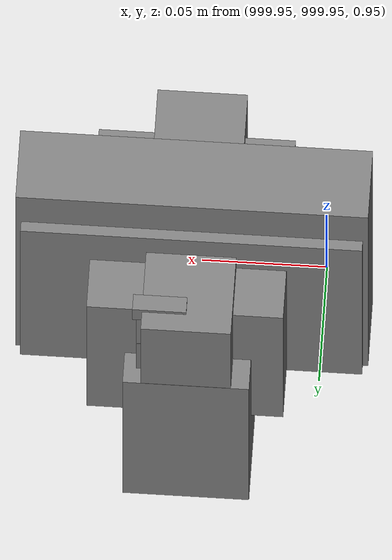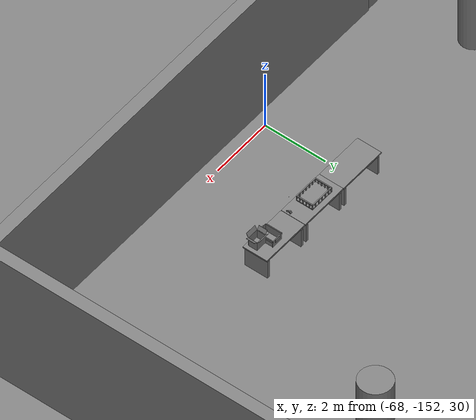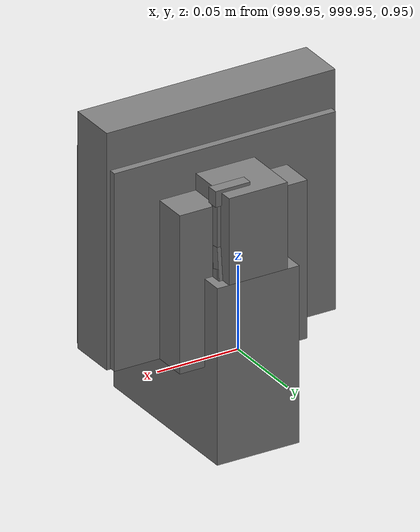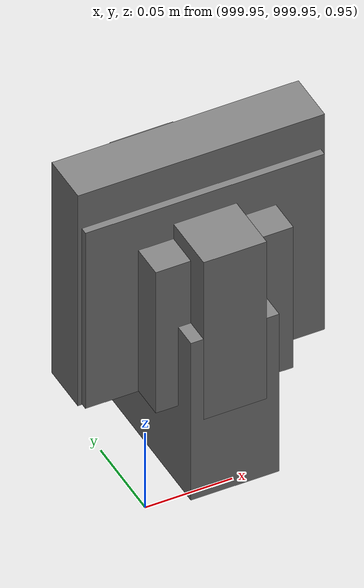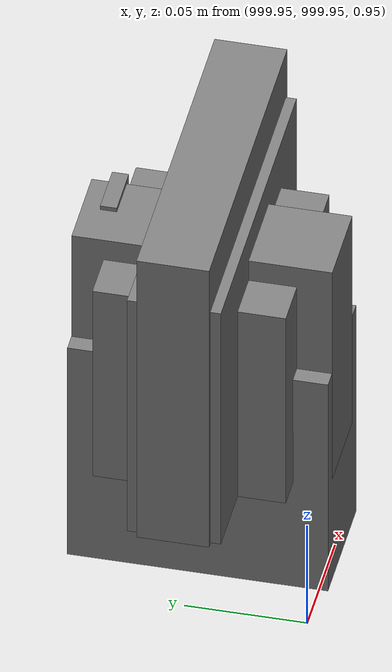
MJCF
<mujoco>
    <option gravity="0.000000000 0.000000000 -9.810000420" timestep="0.0049999999" integrator="implicitfast" density="1.225" viscosity="1.8000001e-05" noslip_iterations="10" iterations="100" sdf_iterations="50">
        <flag multiccd="disable"/>
    </option>
    <size memory="1000M"/>
    <compiler coordinate="local"/>
    <worldbody>
        <light cutoff="30" pos="0 1 1" dir="0 -1 -2"/>
        <light cutoff="30" pos="0 -1 1" dir="0 1 -2"/>
        <body pos="1000.000000000 1000.000000000 1.000000000" euler="0.000000000 0.000000000 180.000000000" name="openloong_gripper_2f85_fix_base_usda_battery_01">
            <geom contype="1" conaffinity="1" density="1000" type="box" material="" rgba="0.500000000 0.500000000 0.500000000 1.000000000" solimp="0.899999976 0.949999988 0.001000000" friction="1.000000000 0.005000000 0.000100000" solref="0.020000000 1.000000000" margin="0" condim="3" group="0" pos="-0.011123657 -0.041940309 0.101691343" quat="1.000000000 0.000000000 0.000000000 0.000000000" size="0.010800000 0.003375000 0.004725000" name="openloong_gripper_2f85_fix_base_usda_geom_EA6AD7A1_5E11_4EAF_8BBA_0A4525733B90"/>
            <geom contype="1" conaffinity="1" density="1000" type="box" material="" rgba="0.500000000 0.500000000 0.500000000 1.000000000" solimp="0.899999976 0.949999988 0.001000000" friction="1.000000000 0.005000000 0.000100000" solref="0.020000000 1.000000000" margin="0" condim="3" group="0" pos="-0.010876465 -0.044247437 0.047066893" quat="0.998702705 -0.050920475 0.000000000 0.000000000" size="0.009450001 0.002700000 0.024975000" name="openloong_gripper_2f85_fix_base_usda_geom_16B601CF_2A03_4F13_9BCA_85AB64A31097"/>
            <geom contype="1" conaffinity="1" density="1000" type="box" material="" rgba="0.500000000 0.500000000 0.500000000 1.000000000" solimp="0.899999976 0.949999988 0.001000000" friction="1.000000000 0.005000000 0.000100000" solref="0.020000000 1.000000000" margin="0" condim="3" group="0" pos="-0.001235962 -0.000659180 0.047381196" quat="1.000000000 0.000000000 0.000000000 0.000000000" size="0.039420001 0.039150000 0.047250003" name="openloong_gripper_2f85_fix_base_usda_geom_090F2EFA_9ED6_4070_ADB3_05E81B104946"/>
            <geom contype="1" conaffinity="1" density="1000" type="box" material="" rgba="0.500000000 0.500000000 0.500000000 1.000000000" solimp="0.899999976 0.949999988 0.001000000" friction="1.000000000 0.005000000 0.000100000" solref="0.020000000 1.000000000" margin="0" condim="3" group="0" pos="-0.010876465 -0.039138794 0.009851727" quat="1.000000000 0.000000000 0.000000000 0.000000000" size="0.009450001 0.010800000 0.013500000" name="openloong_gripper_2f85_fix_base_usda_geom_94BA93D3_E0D1_416D_851B_2E4692DF9108"/>
            <geom contype="1" conaffinity="1" density="1000" type="box" material="" rgba="0.500000000 0.500000000 0.500000000 1.000000000" solimp="0.899999976 0.949999988 0.001000000" friction="1.000000000 0.005000000 0.000100000" solref="0.020000000 1.000000000" margin="0" condim="3" group="0" pos="-0.010876465 -0.041528322 0.071508206" quat="1.000000000 0.000000000 0.000000000 0.000000000" size="0.009450001 0.002700000 0.027000001" name="openloong_gripper_2f85_fix_base_usda_geom_3BF0FED8_66A4_4F11_B1A3_03BC434A4362"/>
            <freejoint name="openloong_gripper_2f85_fix_base_usda_battery_01_joint"/>
            <site size="0.005000000 0.005000000 0.005000000" rgba="0.500000000 0.500000000 0.500000000 1.000000000" pos="0.000000000 0.000000000 0.000000000" quat="0.999961913 0.008726500 0.000000000 0.000000000" group="0" type="sphere" name="openloong_gripper_2f85_fix_base_usda_battery_01site"/>
        </body>
        <body pos="1000.000000000 1000.000000000 1.000000000" euler="0.000000000 0.000000000 180.000000000" name="openloong_gripper_2f85_fix_base_usda_wifi_box">
            <geom contype="1" conaffinity="1" density="1000" type="box" material="" rgba="0.500000000 0.500000000 0.500000000 1.000000000" solimp="0.899999976 0.949999988 0.001000000" friction="1.000000000 0.005000000 0.000100000" solref="0.020000000 1.000000000" margin="0" condim="3" group="0" pos="0.000000000 0.000000000 0.058978677" quat="0.000000000 0.000000047 0.000000000 1.000000000" size="0.068499997 0.018999999 0.059000000" name="openloong_gripper_2f85_fix_base_usda_geom_252C4F45_1726_4281_800C_68AB7F7C0584"/>
            <freejoint name="openloong_gripper_2f85_fix_base_usda_wifi_box_joint"/>
            <site size="0.005000000 0.005000000 0.005000000" rgba="0.500000000 0.500000000 0.500000000 1.000000000" pos="0.000000000 0.000000000 0.000000000" quat="0.999961913 0.008726500 0.000000000 0.000000000" group="0" type="sphere" name="openloong_gripper_2f85_fix_base_usda_wifi_boxsite"/>
        </body>
        <body pos="1000.000000000 1000.000000000 1.000000000" euler="0.000011953 0.000005123 -179.999984741" name="openloong_gripper_2f85_fix_base_usda_intel_box">
            <geom contype="1" conaffinity="1" density="1000" type="box" material="" rgba="0.500000000 0.500000000 0.500000000 1.000000000" solimp="0.899999976 0.949999988 0.001000000" friction="1.000000000 0.005000000 0.000100000" solref="0.020000000 1.000000000" margin="0" condim="3" group="0" pos="0.000000000 -0.000067139 0.000082284" quat="0.707106709 0.000000225 0.000000253 0.707106650" size="0.052800003 0.025300000 0.052800003" name="openloong_gripper_2f85_fix_base_usda_geom_0717C2BF_E80E_401D_BFFD_BDFC756E2FBE"/>
            <freejoint name="openloong_gripper_2f85_fix_base_usda_intel_box_joint"/>
            <site size="0.005000000 0.005000000 0.005000000" rgba="0.500000000 0.500000000 0.500000000 1.000000000" pos="0.000000000 0.000000000 0.000000000" quat="0.999961913 0.008726500 0.000000000 0.000000000" group="0" type="sphere" name="openloong_gripper_2f85_fix_base_usda_intel_boxsite"/>
        </body>
        <body pos="-66.159660339 -149.521881104 31.166709900" euler="-80.908203125 -40.607707977 -80.152931213" mocap="true" name="spotlight3_SpotLight"/>
        <body pos="-66.182815552 -149.173171997 31.169887543" euler="46.032421112 75.572723389 -109.922111511" mocap="true" name="spotlight6_SpotLight"/>
        <body pos="-66.122039795 -148.884246826 31.171957016" euler="-3.123888254 69.468139648 -43.088264465" mocap="true" name="spotlight1_SpotLight"/>
        <body pos="1000.000000000 1000.000000000 1.000000000" euler="0.000000000 0.000000000 180.000000000" name="openloong_gripper_2f85_fix_base_usda_cpu_fan">
            <geom contype="1" conaffinity="1" density="1000" type="box" material="" rgba="0.500000000 0.500000000 0.500000000 1.000000000" solimp="0.899999976 0.949999988 0.001000000" friction="1.000000000 0.005000000 0.000100000" solref="0.020000000 1.000000000" margin="0" condim="3" group="0" pos="0.000000000 0.000000000 0.070034981" quat="0.000000000 0.000000000 0.000000000 1.000000000" size="0.070700005 0.014699999 0.070700005" name="openloong_gripper_2f85_fix_base_usda_geom_2C83596C_F68C_4781_A618_6DC3BEC8BBC0"/>
            <freejoint name="openloong_gripper_2f85_fix_base_usda_cpu_fan_joint"/>
            <site size="0.005000000 0.005000000 0.005000000" rgba="0.500000000 0.500000000 0.500000000 1.000000000" pos="0.000000000 0.000000000 0.000000000" quat="0.999961913 0.008726535 0.000000000 0.000000000" group="0" type="sphere" name="openloong_gripper_2f85_fix_base_usda_cpu_fancsite"/>
        </body>
        <body pos="1000.000000000 999.999938965 1.000000000" euler="0.000000000 0.000000000 180.000000000" name="openloong_gripper_2f85_fix_base_usda_intelcore_i5">
            <geom contype="1" conaffinity="1" density="1000" type="box" material="" rgba="0.500000000 0.500000000 0.500000000 1.000000000" solimp="0.899999976 0.949999988 0.001000000" friction="1.000000000 0.005000000 0.000100000" solref="0.020000000 1.000000000" margin="0" condim="3" group="0" pos="0.000000000 0.000000000 0.051722717" quat="0.707106709 0.000000000 0.000000000 -0.707106769" size="0.052800000 0.018080002 0.052800000" name="openloong_gripper_2f85_fix_base_usda_geom_F359E30F_CC7A_4A1E_8351_210FC19D0656"/>
            <freejoint name="openloong_gripper_2f85_fix_base_usda_intelcore_i5_joint"/>
            <site size="0.005000000 0.005000000 0.005000000" rgba="0.500000000 0.500000000 0.500000000 1.000000000" pos="0.000000000 0.000000000 0.000000000" quat="0.999961913 0.008726534 0.000000000 0.000000000" group="0" type="sphere" name="openloong_gripper_2f85_fix_base_usda_intelcore_i5site"/>
        </body>
        <body pos="-64.866622925 -149.383972168 30.183746338" euler="89.999984741 89.999946594 0.000000000" name="openloong_gripper_2f85_fix_base_usda_bluebox_01">
            <geom contype="1" conaffinity="1" density="1000" type="box" material="" rgba="0.500000000 0.500000000 0.500000000 1.000000000" solimp="0.899999976 0.949999988 0.001000000" friction="1.000000000 0.005000000 0.000100000" solref="0.020000000 1.000000000" margin="0" condim="3" group="0" pos="0.276580811 0.187225342 0.000068665" quat="0.707106948 0.000077471 0.707106352 0.000077486" size="0.100000001 0.057999998 0.010000000" name="openloong_gripper_2f85_fix_base_usda_geom_445EC5D2_C77B_444B_AE69_FD89443D7CC1"/>
            <geom contype="1" conaffinity="1" density="1000" type="box" material="" rgba="0.500000000 0.500000000 0.500000000 1.000000000" solimp="0.899999976 0.949999988 0.001000000" friction="1.000000000 0.005000000 0.000100000" solref="0.020000000 1.000000000" margin="0" condim="3" group="0" pos="0.000000000 0.002883911 0.000000000" quat="0.999999881 0.000000000 0.000000000 0.000000000" size="0.254000008 0.003000000 0.172000006" name="openloong_gripper_2f85_fix_base_usda_geom_EEF77F76_4A4C_4587_8945_C3CC4E36CB0E"/>
            <geom contype="1" conaffinity="1" density="1000" type="box" material="" rgba="0.500000000 0.500000000 0.500000000 1.000000000" solimp="0.899999976 0.949999988 0.001000000" friction="1.000000000 0.005000000 0.000100000" solref="0.020000000 1.000000000" margin="0" condim="3" group="0" pos="0.000000000 0.124874115 0.173484802" quat="0.999796331 0.020176515 -0.000000015 0.000000030" size="0.259999990 0.119999997 0.007000000" name="openloong_gripper_2f85_fix_base_usda_geom_9C1A4F79_2281_41BF_9972_60B6A910A892"/>
            <geom contype="1" conaffinity="1" density="1000" type="box" material="" rgba="0.500000000 0.500000000 0.500000000 1.000000000" solimp="0.899999976 0.949999988 0.001000000" friction="1.000000000 0.005000000 0.000100000" solref="0.020000000 1.000000000" margin="0" condim="3" group="0" pos="0.000000000 0.124874115 -0.173469543" quat="0.999796331 -0.020176545 -0.000000015 0.000000000" size="0.259999990 0.119999997 0.007000000" name="openloong_gripper_2f85_fix_base_usda_geom_90B1996D_DA81_464C_9C59_55D0D11D0A16"/>
            <geom contype="1" conaffinity="1" density="1000" type="box" material="" rgba="0.500000000 0.500000000 0.500000000 1.000000000" solimp="0.899999976 0.949999988 0.001000000" friction="1.000000000 0.005000000 0.000100000" solref="0.020000000 1.000000000" margin="0" condim="3" group="0" pos="0.000000000 0.214008331 0.188980103" quat="0.999912977 0.013176724 0.000000015 0.000000000" size="0.259999990 0.029999999 0.012500000" name="openloong_gripper_2f85_fix_base_usda_geom_311C4930_26F6_43A3_9A7B_C0BD20E63597"/>
            <geom contype="1" conaffinity="1" density="1000" type="box" material="" rgba="0.500000000 0.500000000 0.500000000 1.000000000" solimp="0.899999976 0.949999988 0.001000000" friction="1.000000000 0.005000000 0.000100000" solref="0.020000000 1.000000000" margin="0" condim="3" group="0" pos="-0.258361816 0.125289917 0.001876831" quat="0.702796936 -0.020792112 0.710783124 0.020769298" size="0.189999998 0.119999997 0.009000000" name="openloong_gripper_2f85_fix_base_usda_geom_151F9D8D_933F_40CE_A720_FB4ED72816E1"/>
            <geom contype="1" conaffinity="1" density="1000" type="box" material="" rgba="0.500000000 0.500000000 0.500000000 1.000000000" solimp="0.899999976 0.949999988 0.001000000" friction="1.000000000 0.005000000 0.000100000" solref="0.020000000 1.000000000" margin="0" condim="3" group="0" pos="0.000000000 0.214008331 -0.188980103" quat="0.999912977 -0.013176769 0.000000030 0.000000015" size="0.259999990 0.029999999 0.012500000" name="openloong_gripper_2f85_fix_base_usda_geom_65FCDD46_BD53_4F30_B24A_DFF826131345"/>
            <geom contype="1" conaffinity="1" density="1000" type="box" material="" rgba="0.500000000 0.500000000 0.500000000 1.000000000" solimp="0.899999976 0.949999988 0.001000000" friction="1.000000000 0.005000000 0.000100000" solref="0.020000000 1.000000000" margin="0" condim="3" group="0" pos="-0.276611328 0.187225342 0.000068665" quat="0.707106650 0.000077441 0.707106709 0.000077456" size="0.100000001 0.057999998 0.010000000" name="openloong_gripper_2f85_fix_base_usda_geom_845CEB10_4854_4F93_9B71_6E7CB99F627E"/>
            <geom contype="1" conaffinity="1" density="1000" type="box" material="" rgba="0.500000000 0.500000000 0.500000000 1.000000000" solimp="0.899999976 0.949999988 0.001000000" friction="1.000000000 0.005000000 0.000100000" solref="0.020000000 1.000000000" margin="0" condim="3" group="0" pos="0.258331299 0.125289917 0.001876831" quat="0.702851415 0.018856421 0.710823774 -0.019329369" size="0.189999998 0.119999997 0.009000000" name="openloong_gripper_2f85_fix_base_usda_geom_395D198E_53D2_484C_AC6F_EB6C9E5268F4"/>
            <freejoint name="openloong_gripper_2f85_fix_base_usda_bluebox_01_joint"/>
            <site size="0.005000000 0.005000000 0.005000000" rgba="0.500000000 0.500000000 0.500000000 1.000000000" pos="0.000000000 0.000000000 0.000000000" quat="0.999961913 0.008726534 0.000000000 0.000000000" group="0" type="sphere" name="openloong_gripper_2f85_fix_base_usda_bluebox_01site"/>
        </body>
        <body pos="-64.496299744 -149.491867065 30.235729218" euler="0.000000000 0.000000000 89.999946594" name="openloong_gripper_2f85_fix_base_usda_cardboardbox_01">
            <geom contype="1" conaffinity="1" density="1000" type="box" material="" rgba="0.500000000 0.500000000 0.500000000 1.000000000" solimp="0.899999976 0.949999988 0.001000000" friction="1.000000000 0.005000000 0.000100000" solref="0.020000000 1.000000000" margin="0" condim="3" group="0" pos="-0.003166199 -0.004086494 0.005052090" quat="1.000000000 0.000000000 0.000000000 0.000000000" size="0.142499998 0.177500010 0.005000000" name="openloong_gripper_2f85_fix_base_usda_geom_9F394883_C254_421A_AB52_053D4B568388"/>
            <geom contype="1" conaffinity="1" density="1000" type="box" material="" rgba="0.500000000 0.500000000 0.500000000 1.000000000" solimp="0.899999976 0.949999988 0.001000000" friction="1.000000000 0.005000000 0.000100000" solref="0.020000000 1.000000000" margin="0" condim="3" group="0" pos="-0.003166199 0.170316696 0.150570869" quat="1.000000000 0.000000000 0.000000000 0.000000000" size="0.142499998 0.005000000 0.149999991" name="openloong_gripper_2f85_fix_base_usda_geom_125D6890_ABDF_49D6_AD0E_2085DD6F4A7C"/>
            <geom contype="1" conaffinity="1" density="1000" type="box" material="" rgba="0.500000000 0.500000000 0.500000000 1.000000000" solimp="0.899999976 0.949999988 0.001000000" friction="1.000000000 0.005000000 0.000100000" solref="0.020000000 1.000000000" margin="0" condim="3" group="0" pos="-0.147399902 -0.005307198 0.150570869" quat="1.000000000 0.000000000 0.000000000 0.000000000" size="0.005000000 0.177500010 0.149999991" name="openloong_gripper_2f85_fix_base_usda_geom_AFA2FB56_4FE8_4774_87FE_C5D585552906"/>
            <geom contype="1" conaffinity="1" density="1000" type="box" material="" rgba="0.500000000 0.500000000 0.500000000 1.000000000" solimp="0.899999976 0.949999988 0.001000000" friction="1.000000000 0.005000000 0.000100000" solref="0.020000000 1.000000000" margin="0" condim="3" group="0" pos="0.140275955 -0.005307198 0.150570869" quat="1.000000000 0.000000000 0.000000000 0.000000000" size="0.005000000 0.177500010 0.149999991" name="openloong_gripper_2f85_fix_base_usda_geom_2C43C12E_E84B_4D26_AC0D_723726772569"/>
            <geom contype="1" conaffinity="1" density="1000" type="box" material="" rgba="0.500000000 0.500000000 0.500000000 1.000000000" solimp="0.899999976 0.949999988 0.001000000" friction="1.000000000 0.005000000 0.000100000" solref="0.020000000 1.000000000" margin="0" condim="3" group="0" pos="-0.003166199 -0.181550980 0.150570869" quat="1.000000000 0.000000000 0.000000000 0.000000000" size="0.142499998 0.005000000 0.149999991" name="openloong_gripper_2f85_fix_base_usda_geom_27FFE5D2_A8B6_43F3_B499_0296609835DD"/>
            <freejoint name="openloong_gripper_2f85_fix_base_usda_cardboardbox_01_joint"/>
            <site size="0.005000000 0.005000000 0.005000000" rgba="0.500000000 0.500000000 0.500000000 1.000000000" pos="0.000000000 0.000000000 0.000000000" quat="0.999961913 0.008726535 0.000000000 0.000000000" group="0" type="sphere" name="openloong_gripper_2f85_fix_base_usda_site_662AE5FC_421E_4B69_9E88_35DED4C7CC15"/>
            <body pos="0.139160156 -0.004048347 0.301930904" euler="-179.999954224 49.383502960 179.999954224" name="openloong_gripper_2f85_fix_base_usda_A1_006">
                <geom contype="1" conaffinity="1" density="1000" type="box" material="" rgba="0.500000000 0.500000000 0.500000000 1.000000000" solimp="0.899999976 0.949999988 0.001000000" friction="1.000000000 0.005000000 0.000100000" solref="0.020000000 1.000000000" margin="0" condim="3" group="0" pos="-0.071587563 0.000009537 0.001745224" quat="0.999999881 0.000000000 0.000000000 0.000000000" size="0.071249999 0.179999992 0.002500000" name="openloong_gripper_2f85_fix_base_usda_geom_D6F97FA7_634E_49F5_9150_FDC7B1C797D1"/>
                <joint armature="0" stiffness="0.07" damping="0.0099999998" axis="0.000000 1.000000 0.000000" type="hinge" name="openloong_gripper_2f85_fix_base_usda_A1_006"/>
            </body>
            <body pos="-0.145902634 -0.004086494 0.301938057" euler="-180.000000000 -60.000011444 -180.000000000" name="openloong_gripper_2f85_fix_base_usda_A2_006">
                <geom contype="1" conaffinity="1" density="1000" type="box" material="" rgba="0.500000000 0.500000000 0.500000000 1.000000000" solimp="0.899999976 0.949999988 0.001000000" friction="1.000000000 0.005000000 0.000100000" solref="0.020000000 1.000000000" margin="0" condim="3" group="0" pos="0.071268082 0.000009537 0.002717972" quat="0.000002921 0.000000000 -0.000000030 0.999999881" size="0.071249999 0.179999992 0.002500000" name="openloong_gripper_2f85_fix_base_usda_geom_7EFEF3BE_0759_46DF_9A4E_A36AF1F6BBA1"/>
                <joint armature="0" stiffness="0.07" damping="0.0099999998" axis="0.000000 1.000000 0.000000" type="hinge" name="openloong_gripper_2f85_fix_base_usda_A2_006"/>
            </body>
            <body pos="-0.003385544 0.175991058 0.301930904" euler="-125.858116150 -0.000004561 0.000002331" name="openloong_gripper_2f85_fix_base_usda_B2_006">
                <geom contype="1" conaffinity="1" density="1000" type="box" material="" rgba="0.500000000 0.500000000 0.500000000 1.000000000" solimp="0.899999976 0.949999988 0.001000000" friction="1.000000000 0.005000000 0.000100000" solref="0.020000000 1.000000000" margin="0" condim="3" group="0" pos="0.000009537 -0.070939064 -0.002470016" quat="0.999614120 0.027776197 -0.000000015 0.000000030" size="0.137500003 0.064999998 0.005000000" name="openloong_gripper_2f85_fix_base_usda_geom_479CEDA8_114F_4C17_9CCB_2AEA1B6581F2"/>
                <joint armature="0" stiffness="0.07" damping="0.0099999998" axis="1.000000 0.000000 0.000000" type="hinge" name="openloong_gripper_2f85_fix_base_usda_B2_006"/>
            </body>
            <body pos="-0.003385544 -0.184140205 0.301938057" euler="147.805557251 0.000000000 0.000000000" name="openloong_gripper_2f85_fix_base_usda_B1_006">
                <geom contype="1" conaffinity="1" density="1000" type="box" material="" rgba="0.500000000 0.500000000 0.500000000 1.000000000" solimp="0.899999976 0.949999988 0.001000000" friction="1.000000000 0.005000000 0.000100000" solref="0.020000000 1.000000000" margin="0" condim="3" group="0" pos="-0.000028610 0.070202351 -0.002703667" quat="0.999614179 -0.027776167 0.000000000 0.000000000" size="0.137500003 0.064999998 0.005000000" name="openloong_gripper_2f85_fix_base_usda_geom_EEB921C7_9177_44C3_971B_BA67F90C5B0B"/>
                <joint armature="0" stiffness="0.07" damping="0.0099999998" axis="1.000000 0.000000 0.000000" type="hinge" name="openloong_gripper_2f85_fix_base_usda_B1_006"/>
            </body>
        </body>
        <body pos="-65.882858276 -149.481979370 30.229999542" euler="-64.487716675 0.000000000 0.000000000" name="openloong_gripper_2f85_fix_base_usda_Barcode">
            <geom contype="1" conaffinity="1" density="1000" type="box" material="" rgba="0.500000000 0.500000000 0.500000000 1.000000000" solimp="0.899999976 0.949999988 0.001000000" friction="1.000000000 0.005000000 0.000100000" solref="0.020000000 1.000000000" margin="0" condim="3" group="0" pos="0.000000000 0.013038635 0.001419067" quat="0.000000000 0.000000000 0.000000000 1.000000119" size="0.034000002 0.010000000 0.017999999" name="openloong_gripper_2f85_fix_base_usda_geom_1EB60176_00AC_4D9E_877F_3AD7FBFF83C2"/>
            <geom contype="1" conaffinity="1" density="1000" type="box" material="" rgba="0.500000000 0.500000000 0.500000000 1.000000000" solimp="0.899999976 0.949999988 0.001000000" friction="1.000000000 0.005000000 0.000100000" solref="0.020000000 1.000000000" margin="0" condim="3" group="0" pos="0.000000000 -0.035301208 -0.007095337" quat="0.000000000 0.000000000 -0.043619365 0.999048233" size="0.028999999 0.010000000 0.020000000" name="openloong_gripper_2f85_fix_base_usda_geom_8F02E8A2_DDD5_41C9_9ED6_E866BDA6B36D"/>
            <geom contype="1" conaffinity="1" density="1000" type="box" material="" rgba="0.500000000 0.500000000 0.500000000 1.000000000" solimp="0.899999976 0.949999988 0.001000000" friction="1.000000000 0.005000000 0.000100000" solref="0.020000000 1.000000000" margin="0" condim="3" group="0" pos="0.000000000 -0.043411255 -0.011749268" quat="0.922262907 0.386563420 0.000000000 0.000000000" size="0.026000001 0.010000000 0.020000000" name="openloong_gripper_2f85_fix_base_usda_geom_DC950B6D_4B04_483A_A49E_FAEA845DA8B1"/>
            <geom contype="1" conaffinity="1" density="1000" type="box" material="" rgba="0.500000000 0.500000000 0.500000000 1.000000000" solimp="0.899999976 0.949999988 0.001000000" friction="1.000000000 0.005000000 0.000100000" solref="0.020000000 1.000000000" margin="0" condim="3" group="0" pos="0.000000000 -0.016967773 -0.031860352" quat="0.000000000 0.000000000 0.000000000 1.000000119" size="0.008000000 0.010000000 0.013000000" name="openloong_gripper_2f85_fix_base_usda_geom_E3F2DFA8_EE91_4A6E_8116_CF59BF44C04E"/>
            <geom contype="1" conaffinity="1" density="1000" type="box" material="" rgba="0.500000000 0.500000000 0.500000000 1.000000000" solimp="0.899999976 0.949999988 0.001000000" friction="1.000000000 0.005000000 0.000100000" solref="0.020000000 1.000000000" margin="0" condim="3" group="0" pos="0.000000000 -0.001869202 0.000312805" quat="0.953716993 0.300705761 0.000000000 0.000000000" size="0.032000002 0.010000000 0.018999999" name="openloong_gripper_2f85_fix_base_usda_geom_D9BDDB4A_35A0_4B23_9DEA_9E9419D296A7"/>
            <geom contype="1" conaffinity="1" density="1000" type="box" material="" rgba="0.500000000 0.500000000 0.500000000 1.000000000" solimp="0.899999976 0.949999988 0.001000000" friction="1.000000000 0.005000000 0.000100000" solref="0.020000000 1.000000000" margin="0" condim="3" group="0" pos="0.000000000 -0.019531250 -0.003173828" quat="0.953716993 0.300705761 0.000000000 0.000000000" size="0.030999999 0.010000000 0.020000000" name="openloong_gripper_2f85_fix_base_usda_geom_CA98F225_5CE3_4F3C_BF43_DD4E1ECCD372"/>
            <geom contype="1" conaffinity="1" density="1000" type="box" material="" rgba="0.500000000 0.500000000 0.500000000 1.000000000" solimp="0.899999976 0.949999988 0.001000000" friction="1.000000000 0.005000000 0.000100000" solref="0.020000000 1.000000000" margin="0" condim="3" group="0" pos="0.000000000 -0.035301208 -0.007095337" quat="0.953716993 0.300705761 0.000000000 0.000000000" size="0.028999999 0.010000000 0.020000000" name="openloong_gripper_2f85_fix_base_usda_geom_CA6BDDB5_8FDD_46E7_AA08_850E9B1225A6"/>
            <geom contype="1" conaffinity="1" density="1000" type="box" material="" rgba="0.500000000 0.500000000 0.500000000 1.000000000" solimp="0.899999976 0.949999988 0.001000000" friction="1.000000000 0.005000000 0.000100000" solref="0.020000000 1.000000000" margin="0" condim="3" group="0" pos="0.000000000 -0.042617798 -0.071121216" quat="0.000000000 0.000000000 0.000000000 1.000000119" size="0.013000000 0.021000000 0.059999999" name="openloong_gripper_2f85_fix_base_usda_geom_D9AE4871_0267_4D3D_B155_775A58B22B8B"/>
            <freejoint name="openloong_gripper_2f85_fix_base_usda_Barcode_joint"/>
            <site size="0.005000000 0.005000000 0.005000000" rgba="0.500000000 0.500000000 0.500000000 1.000000000" pos="0.000000000 0.000000000 0.000000000" quat="1.000000000 0.000000000 0.000000000 0.000000000" group="0" type="sphere" name="openloong_gripper_2f85_fix_base_usda_Barcode_site"/>
        </body>
        <body pos="-66.745018005 -149.392349243 30.184000015" euler="0.000000000 0.000000000 89.999946594" name="[22329965968814]_Basket_01">
            <geom contype="1" conaffinity="1" density="1000" type="box" material="" rgba="0.500000000 0.500000000 0.500000000 1.000000000" solimp="0.899999976 0.949999988 0.001000000" friction="1.000000000 0.005000000 0.000100000" solref="0.020000000 1.000000000" margin="0" condim="3" group="0" pos="-0.052425385 0.389207840 0.089787483" quat="0.707107008 0.000000000 0.000000000 0.707106411" size="0.014249999 0.014249999 0.059999999" name="[22329965968814]_geom_EF24B55D_AB91_465E_BEAE_A24C10F919CA"/>
            <geom contype="1" conaffinity="1" density="1000" type="box" material="" rgba="0.500000000 0.500000000 0.500000000 1.000000000" solimp="0.899999976 0.949999988 0.001000000" friction="1.000000000 0.005000000 0.000100000" solref="0.020000000 1.000000000" margin="0" condim="3" group="0" pos="0.264015198 -0.133043289 0.089787483" quat="0.707107008 0.000000000 0.000000000 0.707106411" size="0.014249999 0.014249999 0.059999999" name="[22329965968814]_geom_7C1D4664_C5E5_4032_B6FA_C9C0E0167607"/>
            <geom contype="1" conaffinity="1" density="1000" type="box" material="" rgba="0.500000000 0.500000000 0.500000000 1.000000000" solimp="0.899999976 0.949999988 0.001000000" friction="1.000000000 0.005000000 0.000100000" solref="0.020000000 1.000000000" margin="0" condim="3" group="0" pos="-0.264015198 -0.265548706 0.089793205" quat="0.707107008 0.000000000 0.000000000 0.707106411" size="0.014249999 0.014249999 0.059999999" name="[22329965968814]_geom_0B635639_5D34_4661_ABF8_4A248A6D711C"/>
            <geom contype="1" conaffinity="1" density="1000" type="box" material="" rgba="0.500000000 0.500000000 0.500000000 1.000000000" solimp="0.899999976 0.949999988 0.001000000" friction="1.000000000 0.005000000 0.000100000" solref="0.020000000 1.000000000" margin="0" condim="3" group="0" pos="-0.160263062 -0.389322281 0.089793205" quat="0.707107008 0.000000000 0.000000000 0.707106411" size="0.014249999 0.014249999 0.059999999" name="[22329965968814]_geom_B3562A54_1282_4D82_98F6_F043E3AFF928"/>
            <geom contype="1" conaffinity="1" density="1000" type="box" material="" rgba="0.500000000 0.500000000 0.500000000 1.000000000" solimp="0.899999976 0.949999988 0.001000000" friction="1.000000000 0.005000000 0.000100000" solref="0.020000000 1.000000000" margin="0" condim="3" group="0" pos="0.162265778 -0.389322281 0.089787483" quat="0.707107008 0.000000000 0.000000000 0.707106411" size="0.014249999 0.014249999 0.059999999" name="[22329965968814]_geom_7FA26040_47C0_456C_809A_A141E073F655"/>
            <geom contype="1" conaffinity="1" density="1000" type="box" material="" rgba="0.500000000 0.500000000 0.500000000 1.000000000" solimp="0.899999976 0.949999988 0.001000000" friction="1.000000000 0.005000000 0.000100000" solref="0.020000000 1.000000000" margin="0" condim="3" group="0" pos="0.264015198 0.389207840 0.089787483" quat="0.707107008 0.000000000 0.000000000 0.707106411" size="0.014249999 0.014249999 0.059999999" name="[22329965968814]_geom_D4797AA7_79DD_4129_B6D3_F8049236646E"/>
            <geom contype="1" conaffinity="1" density="1000" type="box" material="" rgba="0.500000000 0.500000000 0.500000000 1.000000000" solimp="0.899999976 0.949999988 0.001000000" friction="1.000000000 0.005000000 0.000100000" solref="0.020000000 1.000000000" margin="0" condim="3" group="0" pos="-0.264015198 -0.133043289 0.089793205" quat="0.707107008 0.000000000 0.000000000 0.707106411" size="0.014249999 0.014249999 0.059999999" name="[22329965968814]_geom_7D2094F3_70E4_447C_93A6_C804BD22E1A0"/>
            <geom contype="1" conaffinity="1" density="1000" type="box" material="" rgba="0.500000000 0.500000000 0.500000000 1.000000000" solimp="0.899999976 0.949999988 0.001000000" friction="1.000000000 0.005000000 0.000100000" solref="0.020000000 1.000000000" margin="0" condim="3" group="0" pos="-0.264026642 0.269256592 0.089793205" quat="0.707107008 0.000000000 0.000000000 0.707106411" size="0.014249999 0.014249999 0.059999999" name="[22329965968814]_geom_B7A7B453_B0DD_4378_A46D_EA5111336BC3"/>
            <geom contype="1" conaffinity="1" density="1000" type="box" material="" rgba="0.500000000 0.500000000 0.500000000 1.000000000" solimp="0.899999976 0.949999988 0.001000000" friction="1.000000000 0.005000000 0.000100000" solref="0.020000000 1.000000000" margin="0" condim="3" group="0" pos="0.054462433 0.389207840 0.089787483" quat="0.707107008 0.000000000 0.000000000 0.707106411" size="0.014249999 0.014249999 0.059999999" name="[22329965968814]_geom_631F1344_CC99_4BD4_9D76_4DD4EB8EC8DB"/>
            <geom contype="1" conaffinity="1" density="1000" type="box" material="" rgba="0.500000000 0.500000000 0.500000000 1.000000000" solimp="0.899999976 0.949999988 0.001000000" friction="1.000000000 0.005000000 0.000100000" solref="0.020000000 1.000000000" margin="0" condim="3" group="0" pos="0.054462433 -0.389322281 0.089787483" quat="0.707107008 0.000000000 0.000000000 0.707106411" size="0.014249999 0.014249999 0.059999999" name="[22329965968814]_geom_B399B6C3_F06A_429B_8466_3124BD7E3571"/>
            <geom contype="1" conaffinity="1" density="1000" type="box" material="" rgba="0.500000000 0.500000000 0.500000000 1.000000000" solimp="0.899999976 0.949999988 0.001000000" friction="1.000000000 0.005000000 0.000100000" solref="0.020000000 1.000000000" margin="0" condim="3" group="0" pos="0.264015198 0.269256592 0.089793205" quat="0.707107008 0.000000000 0.000000000 0.707106411" size="0.014249999 0.014249999 0.059999999" name="[22329965968814]_geom_CACABDB0_1BA2_4513_9A8C_45DD016AC8B0"/>
            <geom contype="1" conaffinity="1" density="1000" type="box" material="" rgba="0.500000000 0.500000000 0.500000000 1.000000000" solimp="0.899999976 0.949999988 0.001000000" friction="1.000000000 0.005000000 0.000100000" solref="0.020000000 1.000000000" margin="0" condim="3" group="0" pos="0.264015198 -0.389322281 0.089787483" quat="0.707107008 0.000000000 0.000000000 0.707106411" size="0.014249999 0.014249999 0.059999999" name="[22329965968814]_geom_2770304A_1FC4_4D41_9749_616DF2A4E282"/>
            <geom contype="1" conaffinity="1" density="1000" type="box" material="" rgba="0.500000000 0.500000000 0.500000000 1.000000000" solimp="0.899999976 0.949999988 0.001000000" friction="1.000000000 0.005000000 0.000100000" solref="0.020000000 1.000000000" margin="0" condim="3" group="0" pos="0.000000000 0.000000000 0.015998840" quat="0.707107008 0.000000000 0.000000000 0.707106411" size="0.403499991 0.279000014 0.015750000" name="[22329965968814]_geom_5D7B96A9_083E_4F23_9AB8_A3448598B4C9"/>
            <geom contype="1" conaffinity="1" density="1000" type="box" material="" rgba="0.500000000 0.500000000 0.500000000 1.000000000" solimp="0.899999976 0.949999988 0.001000000" friction="1.000000000 0.005000000 0.000100000" solref="0.020000000 1.000000000" margin="0" condim="3" group="0" pos="0.000000000 -0.389476776 0.163619041" quat="0.707107008 0.000000000 0.000000000 0.707106411" size="0.015000000 0.277500004 0.015750000" name="[22329965968814]_geom_81E041AE_B2FD_4202_89FF_8C9C29C743BF"/>
            <geom contype="1" conaffinity="1" density="1000" type="box" material="" rgba="0.500000000 0.500000000 0.500000000 1.000000000" solimp="0.899999976 0.949999988 0.001000000" friction="1.000000000 0.005000000 0.000100000" solref="0.020000000 1.000000000" margin="0" condim="3" group="0" pos="0.162265778 0.389207840 0.089787483" quat="0.707107008 0.000000000 0.000000000 0.707106411" size="0.014249999 0.014249999 0.059999999" name="[22329965968814]_geom_6DB8407C_D5F2_49EE_A6E1_C49D109939BD"/>
            <geom contype="1" conaffinity="1" density="1000" type="box" material="" rgba="0.500000000 0.500000000 0.500000000 1.000000000" solimp="0.899999976 0.949999988 0.001000000" friction="1.000000000 0.005000000 0.000100000" solref="0.020000000 1.000000000" margin="0" condim="3" group="0" pos="0.000000000 0.389471054 0.163619041" quat="0.707107008 0.000000000 0.000000000 0.707106411" size="0.015000000 0.277500004 0.015750000" name="[22329965968814]_geom_8676CF1F_E57B_491D_A8BD_F80E120F15A4"/>
            <geom contype="1" conaffinity="1" density="1000" type="box" material="" rgba="0.500000000 0.500000000 0.500000000 1.000000000" solimp="0.899999976 0.949999988 0.001000000" friction="1.000000000 0.005000000 0.000100000" solref="0.020000000 1.000000000" margin="0" condim="3" group="0" pos="-0.263511658 0.000000000 0.163619041" quat="0.707107008 0.000000000 0.000000000 0.707106411" size="0.403499991 0.015000000 0.015750000" name="[22329965968814]_geom_C145F587_CDD8_49D2_BB4C_2827CB2D41F4"/>
            <geom contype="1" conaffinity="1" density="1000" type="box" material="" rgba="0.500000000 0.500000000 0.500000000 1.000000000" solimp="0.899999976 0.949999988 0.001000000" friction="1.000000000 0.005000000 0.000100000" solref="0.020000000 1.000000000" margin="0" condim="3" group="0" pos="-0.264015198 0.141334534 0.089793205" quat="0.707107008 0.000000000 0.000000000 0.707106411" size="0.014249999 0.014249999 0.059999999" name="[22329965968814]_geom_2488AC05_6281_4FE9_BD85_E1B127668B30"/>
            <geom contype="1" conaffinity="1" density="1000" type="box" material="" rgba="0.500000000 0.500000000 0.500000000 1.000000000" solimp="0.899999976 0.949999988 0.001000000" friction="1.000000000 0.005000000 0.000100000" solref="0.020000000 1.000000000" margin="0" condim="3" group="0" pos="0.264015198 -0.265548706 0.089787483" quat="0.707107008 0.000000000 0.000000000 0.707106411" size="0.014249999 0.014249999 0.059999999" name="[22329965968814]_geom_B6B94A09_CE73_4E5D_BF66_AB603381C0DE"/>
            <geom contype="1" conaffinity="1" density="1000" type="box" material="" rgba="0.500000000 0.500000000 0.500000000 1.000000000" solimp="0.899999976 0.949999988 0.001000000" friction="1.000000000 0.005000000 0.000100000" solref="0.020000000 1.000000000" margin="0" condim="3" group="0" pos="-0.160263062 0.389207840 0.089787483" quat="0.707107008 0.000000000 0.000000000 0.707106411" size="0.014249999 0.014249999 0.059999999" name="[22329965968814]_geom_FE64E5C9_0799_4EFA_830C_0AFB760A302F"/>
            <geom contype="1" conaffinity="1" density="1000" type="box" material="" rgba="0.500000000 0.500000000 0.500000000 1.000000000" solimp="0.899999976 0.949999988 0.001000000" friction="1.000000000 0.005000000 0.000100000" solref="0.020000000 1.000000000" margin="0" condim="3" group="0" pos="-0.052425385 -0.389322281 0.089787483" quat="0.707107008 0.000000000 0.000000000 0.707106411" size="0.014249999 0.014249999 0.059999999" name="[22329965968814]_geom_B0A3B0D6_398C_421B_BB98_140CB41A624D"/>
            <geom contype="1" conaffinity="1" density="1000" type="box" material="" rgba="0.500000000 0.500000000 0.500000000 1.000000000" solimp="0.899999976 0.949999988 0.001000000" friction="1.000000000 0.005000000 0.000100000" solref="0.020000000 1.000000000" margin="0" condim="3" group="0" pos="-0.264026642 -0.389322281 0.089793205" quat="0.707107008 0.000000000 0.000000000 0.707106411" size="0.014249999 0.014249999 0.059999999" name="[22329965968814]_geom_1ED1515A_BE1E_48C2_988B_504E62B1842D"/>
            <geom contype="1" conaffinity="1" density="1000" type="box" material="" rgba="0.500000000 0.500000000 0.500000000 1.000000000" solimp="0.899999976 0.949999988 0.001000000" friction="1.000000000 0.005000000 0.000100000" solref="0.020000000 1.000000000" margin="0" condim="3" group="0" pos="0.264015198 0.141334534 0.089787483" quat="0.707107008 0.000000000 0.000000000 0.707106411" size="0.014249999 0.014249999 0.059999999" name="[22329965968814]_geom_A33947E0_6D14_4440_ACA3_E7CA236A0D10"/>
            <geom contype="1" conaffinity="1" density="1000" type="box" material="" rgba="0.500000000 0.500000000 0.500000000 1.000000000" solimp="0.899999976 0.949999988 0.001000000" friction="1.000000000 0.005000000 0.000100000" solref="0.020000000 1.000000000" margin="0" condim="3" group="0" pos="-0.264015198 0.389207840 0.089793205" quat="0.707107008 0.000000000 0.000000000 0.707106411" size="0.014249999 0.014249999 0.059999999" name="[22329965968814]_geom_54AE011A_ABBA_4CCA_97AD_FF63B8CF26E5"/>
            <geom contype="1" conaffinity="1" density="1000" type="box" material="" rgba="0.500000000 0.500000000 0.500000000 1.000000000" solimp="0.899999976 0.949999988 0.001000000" friction="1.000000000 0.005000000 0.000100000" solref="0.020000000 1.000000000" margin="0" condim="3" group="0" pos="0.264015198 0.004480362 0.089787483" quat="0.707107008 0.000000000 0.000000000 0.707106411" size="0.014249999 0.014249999 0.059999999" name="[22329965968814]_geom_75889680_612A_4C81_AAF1_41250E15F5C9"/>
            <geom contype="1" conaffinity="1" density="1000" type="box" material="" rgba="0.500000000 0.500000000 0.500000000 1.000000000" solimp="0.899999976 0.949999988 0.001000000" friction="1.000000000 0.005000000 0.000100000" solref="0.020000000 1.000000000" margin="0" condim="3" group="0" pos="0.263694763 -0.000011444 0.163619041" quat="0.707107008 0.000000000 0.000000000 0.707106411" size="0.403499991 0.015000000 0.015750000" name="[22329965968814]_geom_CFB3CABF_12C1_4ED0_952F_4C847A9936A6"/>
            <geom contype="1" conaffinity="1" density="1000" type="box" material="" rgba="0.500000000 0.500000000 0.500000000 1.000000000" solimp="0.899999976 0.949999988 0.001000000" friction="1.000000000 0.005000000 0.000100000" solref="0.020000000 1.000000000" margin="0" condim="3" group="0" pos="-0.264015198 0.004480362 0.089793205" quat="0.707107008 0.000000000 0.000000000 0.707106411" size="0.014249999 0.014249999 0.059999999" name="[22329965968814]_geom_900A60B8_32B4_4E65_8259_181476F85F0E"/>
            <freejoint name="[22329965968814]_joint_D062E7E7_7097_48B6_9CA3_9C4E7E4B0548"/>
        </body>
        <body pos="0.000000000 0.000000000 0.000000000" euler="0.000000000 0.000000000 0.000000000" name="Static Objects_Static Objects">
            <geom contype="1" conaffinity="1" density="1000" type="box" material="" rgba="0.500000000 0.500000000 0.500000000 1.000000000" solimp="0.899999976 0.949999988 0.001000000" friction="1.000000000 0.005000000 0.000100000" solref="0.020000000 1.000000000" margin="0" condim="3" group="0" pos="-67.544113159 -149.365814209 29.727830887" quat="0.500000417 0.499999970 0.499999553 0.499999970" size="0.381000012 0.319999993 0.041000001" name="Static Objects_geom_322FC2D4_7DEA_4082_918D_2AC3BE189B22"/>
            <geom contype="1" conaffinity="1" density="1000" type="box" material="" rgba="0.500000000 0.500000000 0.500000000 1.000000000" solimp="0.899999976 0.949999988 0.001000000" friction="1.000000000 0.005000000 0.000100000" solref="0.020000000 1.000000000" margin="0" condim="3" group="0" pos="-68.239501953 -149.365814209 30.086868286" quat="0.500000417 0.499999970 0.499999553 0.499999970" size="0.370999992 0.039500002 0.745000005" name="Static Objects_geom_664AE48A_73F2_43C1_B105_1F8F8D8BD694"/>
            <geom contype="1" conaffinity="1" density="1000" type="box" material="" rgba="0.500000000 0.500000000 0.500000000 1.000000000" solimp="0.899999976 0.949999988 0.001000000" friction="1.000000000 0.005000000 0.000100000" solref="0.020000000 1.000000000" margin="0" condim="3" group="0" pos="-68.239501953 -149.365814209 30.147235870" quat="0.500000417 0.499999970 0.499999553 0.499999970" size="0.400000006 0.022000000 0.800000012" name="Static Objects_geom_89D1A71F_726E_4827_BE3D_3EFFF6F98C91"/>
            <geom contype="1" conaffinity="1" density="1000" type="box" material="" rgba="0.500000000 0.500000000 0.500000000 1.000000000" solimp="0.899999976 0.949999988 0.001000000" friction="1.000000000 0.005000000 0.000100000" solref="0.020000000 1.000000000" margin="0" condim="3" group="0" pos="-68.934890747 -149.365814209 29.727830887" quat="0.500000417 0.499999970 0.499999553 0.499999970" size="0.381000012 0.319999993 0.041000001" name="Static Objects_geom_E0C7E72F_9645_4520_8F2E_782F4FA4389A"/>
            <geom contype="1" conaffinity="1" density="1000" type="box" material="" rgba="0.500000000 0.500000000 0.500000000 1.000000000" solimp="0.899999976 0.949999988 0.001000000" friction="1.000000000 0.005000000 0.000100000" solref="0.020000000 1.000000000" margin="0" condim="3" group="0" pos="-68.239501953 -149.365814209 29.561563492" quat="0.500000417 0.499999970 0.499999553 0.499999970" size="0.020000000 0.022000000 0.660000026" name="Static Objects_geom_C4BC2727_E6D1_4358_BCC6_05349A233794"/>
            <geom contype="1" conaffinity="1" density="1000" type="box" material="" rgba="0.500000000 0.500000000 0.500000000 1.000000000" solimp="0.899999976 0.949999988 0.001000000" friction="1.000000000 0.005000000 0.000100000" solref="0.020000000 1.000000000" margin="0" condim="3" group="0" pos="-65.945671082 -149.365814209 29.727830887" quat="0.500000417 0.499999970 0.499999553 0.499999970" size="0.381000012 0.319999993 0.041000001" name="Static Objects_geom_64231BC5_5806_4F5E_A29C_2EFDAB224572"/>
            <geom contype="1" conaffinity="1" density="1000" type="box" material="" rgba="0.500000000 0.500000000 0.500000000 1.000000000" solimp="0.899999976 0.949999988 0.001000000" friction="1.000000000 0.005000000 0.000100000" solref="0.020000000 1.000000000" margin="0" condim="3" group="0" pos="-66.641059875 -149.365814209 30.086868286" quat="0.500000417 0.499999970 0.499999553 0.499999970" size="0.370999992 0.039500002 0.745000005" name="Static Objects_geom_DF22FBC9_C95B_4F30_AC14_2D872E4FD543"/>
            <geom contype="1" conaffinity="1" density="1000" type="box" material="" rgba="0.500000000 0.500000000 0.500000000 1.000000000" solimp="0.899999976 0.949999988 0.001000000" friction="1.000000000 0.005000000 0.000100000" solref="0.020000000 1.000000000" margin="0" condim="3" group="0" pos="-66.641059875 -149.365814209 30.147235870" quat="0.500000417 0.499999970 0.499999553 0.499999970" size="0.400000006 0.022000000 0.800000012" name="Static Objects_geom_2A777681_D75F_42D3_8FAE_EE6B22E895EF"/>
            <geom contype="1" conaffinity="1" density="1000" type="box" material="" rgba="0.500000000 0.500000000 0.500000000 1.000000000" solimp="0.899999976 0.949999988 0.001000000" friction="1.000000000 0.005000000 0.000100000" solref="0.020000000 1.000000000" margin="0" condim="3" group="0" pos="-67.336448669 -149.365814209 29.727830887" quat="0.500000417 0.499999970 0.499999553 0.499999970" size="0.381000012 0.319999993 0.041000001" name="Static Objects_geom_A2B8CBAC_7566_4936_B5C7_4F07FB605CBA"/>
            <geom contype="1" conaffinity="1" density="1000" type="box" material="" rgba="0.500000000 0.500000000 0.500000000 1.000000000" solimp="0.899999976 0.949999988 0.001000000" friction="1.000000000 0.005000000 0.000100000" solref="0.020000000 1.000000000" margin="0" condim="3" group="0" pos="-66.641059875 -149.365814209 29.561563492" quat="0.500000417 0.499999970 0.499999553 0.499999970" size="0.020000000 0.022000000 0.660000026" name="Static Objects_geom_63459F8D_B5CC_4F4C_9E97_6E30B7080884"/>
            <geom contype="1" conaffinity="1" density="1000" type="box" material="" rgba="0.500000000 0.500000000 0.500000000 1.000000000" solimp="0.899999976 0.949999988 0.001000000" friction="1.000000000 0.005000000 0.000100000" solref="0.020000000 1.000000000" margin="0" condim="3" group="0" pos="-64.338577271 -149.365814209 29.727830887" quat="0.500000417 0.499999970 0.499999553 0.499999970" size="0.381000012 0.319999993 0.041000001" name="Static Objects_geom_871E9DC6_4240_4134_B600_9B02C6D12364"/>
            <geom contype="1" conaffinity="1" density="1000" type="box" material="" rgba="0.500000000 0.500000000 0.500000000 1.000000000" solimp="0.899999976 0.949999988 0.001000000" friction="1.000000000 0.005000000 0.000100000" solref="0.020000000 1.000000000" margin="0" condim="3" group="0" pos="-65.033966064 -149.365814209 30.086868286" quat="0.500000417 0.499999970 0.499999553 0.499999970" size="0.370999992 0.039500002 0.745000005" name="Static Objects_geom_51C6CB82_FF57_4104_A58B_373C4014CCFB"/>
            <geom contype="1" conaffinity="1" density="1000" type="box" material="" rgba="0.500000000 0.500000000 0.500000000 1.000000000" solimp="0.899999976 0.949999988 0.001000000" friction="1.000000000 0.005000000 0.000100000" solref="0.020000000 1.000000000" margin="0" condim="3" group="0" pos="-65.033966064 -149.365814209 30.147235870" quat="0.500000417 0.499999970 0.499999553 0.499999970" size="0.400000006 0.022000000 0.800000012" name="Static Objects_geom_BA594C01_9FD2_43E4_88C7_28F082AF3E4B"/>
            <geom contype="1" conaffinity="1" density="1000" type="box" material="" rgba="0.500000000 0.500000000 0.500000000 1.000000000" solimp="0.899999976 0.949999988 0.001000000" friction="1.000000000 0.005000000 0.000100000" solref="0.020000000 1.000000000" margin="0" condim="3" group="0" pos="-65.729354858 -149.365814209 29.727830887" quat="0.500000417 0.499999970 0.499999553 0.499999970" size="0.381000012 0.319999993 0.041000001" name="Static Objects_geom_4235EC95_2A5C_409D_A86C_DA11AAEDF4D2"/>
            <geom contype="1" conaffinity="1" density="1000" type="box" material="" rgba="0.500000000 0.500000000 0.500000000 1.000000000" solimp="0.899999976 0.949999988 0.001000000" friction="1.000000000 0.005000000 0.000100000" solref="0.020000000 1.000000000" margin="0" condim="3" group="0" pos="-65.033966064 -149.365814209 29.561563492" quat="0.500000417 0.499999970 0.499999553 0.499999970" size="0.020000000 0.022000000 0.660000026" name="Static Objects_geom_E24A8DE0_73FB_4F1A_B2F5_5E0F7E4B8657"/>
            <geom contype="1" conaffinity="1" density="1000" type="box" material="" rgba="0.500000000 0.500000000 0.500000000 1.000000000" solimp="0.899999976 0.949999988 0.001000000" friction="1.000000000 0.005000000 0.000100000" solref="0.020000000 1.000000000" margin="0" condim="3" group="0" pos="-61.754566193 -137.853729248 33.906845093" quat="0.707107067 0.000000000 0.000000000 0.707106471" size="0.759999990 0.759999990 4.500000000" name="Static Objects_geom_C318159E_A804_470B_A771_AC2848BE8113"/>
            <geom contype="1" conaffinity="1" density="1000" type="box" material="" rgba="0.500000000 0.500000000 0.500000000 1.000000000" solimp="0.899999976 0.949999988 0.001000000" friction="1.000000000 0.005000000 0.000100000" solref="0.020000000 1.000000000" margin="0" condim="3" group="0" pos="-57.511135101 -144.927108765 31.707921982" quat="1.000000000 0.000000000 0.000000000 0.000000000" size="0.200000003 8.000000000 2.299999952" name="Static Objects_geom_FD1EA28A_5F9A_43C3_98C4_48CDF654D13E"/>
            <geom contype="1" conaffinity="1" density="1000" type="box" material="" rgba="0.500000000 0.500000000 0.500000000 1.000000000" solimp="0.899999976 0.949999988 0.001000000" friction="1.000000000 0.005000000 0.000100000" solref="0.020000000 1.000000000" margin="0" condim="3" group="0" pos="-80.517646790 -157.574050903 31.688196182" quat="0.707107067 0.000000000 0.000000000 0.707106471" size="0.600000024 0.600000024 2.299999952" name="Static Objects_geom_3AA86BFD_DE87_452C_8BB4_439B0E044DF1"/>
            <geom contype="1" conaffinity="1" density="1000" type="box" material="" rgba="0.500000000 0.500000000 0.500000000 1.000000000" solimp="0.899999976 0.949999988 0.001000000" friction="1.000000000 0.005000000 0.000100000" solref="0.020000000 1.000000000" margin="0" condim="3" group="0" pos="-80.711044312 -147.414932251 31.666158676" quat="1.000000000 0.000000000 0.000000000 0.000000000" size="0.200000003 10.000000000 2.299999952" name="Static Objects_geom_D08E86F1_95C6_48EA_A14C_45D801DA541F"/>
            <geom contype="1" conaffinity="1" density="1000" type="box" material="" rgba="0.500000000 0.500000000 0.500000000 1.000000000" solimp="0.899999976 0.949999988 0.001000000" friction="1.000000000 0.005000000 0.000100000" solref="0.020000000 1.000000000" margin="0" condim="3" group="0" pos="-57.687217712 -137.434692383 31.688196182" quat="0.707107067 0.000000000 0.000000000 0.707106471" size="0.600000024 0.600000024 2.299999952" name="Static Objects_geom_2F3F5A10_B595_4B32_9720_CBF9E9C4A772"/>
            <geom contype="1" conaffinity="1" density="1000" type="box" material="" rgba="0.500000000 0.500000000 0.500000000 1.000000000" solimp="0.899999976 0.949999988 0.001000000" friction="1.000000000 0.005000000 0.000100000" solref="0.020000000 1.000000000" margin="0" condim="3" group="0" pos="-69.537033081 -140.263229370 31.714921951" quat="0.707107067 0.000000000 0.000000000 0.707106471" size="0.759999990 4.500000000 2.299999952" name="Static Objects_geom_BEF26C27_BC38_4D07_A861_F4A2844BF28F"/>
            <geom contype="1" conaffinity="1" density="1000" type="box" material="" rgba="0.500000000 0.500000000 0.500000000 1.000000000" solimp="0.899999976 0.949999988 0.001000000" friction="1.000000000 0.005000000 0.000100000" solref="0.020000000 1.000000000" margin="0" condim="3" group="0" pos="-80.073638916 -137.853713989 33.906845093" quat="0.707107067 0.000000000 0.000000000 0.707106471" size="0.759999990 0.759999990 4.500000000" name="Static Objects_geom_35482474_E00A_439D_8BB6_BDDC9B8711D5"/>
            <geom contype="1" conaffinity="1" density="1000" type="box" material="" rgba="0.500000000 0.500000000 0.500000000 1.000000000" solimp="0.899999976 0.949999988 0.001000000" friction="1.000000000 0.005000000 0.000100000" solref="0.020000000 1.000000000" margin="0" condim="3" group="0" pos="-73.406707764 -155.734664917 31.707921982" quat="1.000000000 0.000000000 0.000000000 0.000000000" size="0.200000003 3.000000000 2.299999952" name="Static Objects_geom_ACC1ADE6_C08E_4300_B3CD_F5FFB0ED5328"/>
            <geom contype="1" conaffinity="1" density="1000" type="box" material="" rgba="0.500000000 0.500000000 0.500000000 1.000000000" solimp="0.899999976 0.949999988 0.001000000" friction="1.000000000 0.005000000 0.000100000" solref="0.020000000 1.000000000" margin="0" condim="3" group="0" pos="-68.497543335 -137.448257446 31.707921982" quat="0.707107067 0.000000000 0.000000000 0.707106471" size="0.200000003 14.000000000 2.299999952" name="Static Objects_geom_D338C535_EFA7_4257_A365_0D2CEE0FAAC3"/>
            <geom contype="1" conaffinity="1" density="1000" type="cylinder" material="" rgba="0.500000000 0.500000000 0.500000000 1.000000000" solimp="0.899999976 0.949999988 0.001000000" friction="1.000000000 0.005000000 0.000100000" solref="0.020000000 1.000000000" margin="0" condim="3" group="0" pos="-68.868522644 -142.134506226 31.711090088" quat="0.707107067 0.000000000 0.000000000 0.707106471" size="0.509999990 2.299999952 1.000000000" name="Static Objects_geom_052A2A67_54DF_4B6C_BF5A_1FF80D804713"/>
            <geom contype="1" conaffinity="1" density="1000" type="plane" material="" rgba="0.500000000 0.500000000 0.500000000 1.000000000" solimp="0.899999976 0.949999988 0.001000000" friction="1.000000000 0.005000000 0.000100000" solref="0.020000000 1.000000000" margin="0" condim="3" group="0" pos="-72.873703003 -147.131927490 29.409669876" quat="1.000000000 0.000000000 0.000000000 0.000000000" size="18.000000000 14.000000000 1.000000000" name="Static Objects_geom_FCB255BC_D94F_42DB_8DC8_CE75FAB56EA0"/>
            <geom contype="1" conaffinity="1" density="1000" type="box" material="" rgba="0.500000000 0.500000000 0.500000000 1.000000000" solimp="0.899999976 0.949999988 0.001000000" friction="1.000000000 0.005000000 0.000100000" solref="0.020000000 1.000000000" margin="0" condim="3" group="0" pos="-79.943580627 -157.782272339 31.707921982" quat="0.707107067 0.000000000 0.000000000 0.707106471" size="0.200000003 7.000000000 2.299999952" name="Static Objects_geom_68FF45A2_D7B7_4789_B647_062C9B99F5A1"/>
            <geom contype="1" conaffinity="1" density="1000" type="box" material="" rgba="0.500000000 0.500000000 0.500000000 1.000000000" solimp="0.899999976 0.949999988 0.001000000" friction="1.000000000 0.005000000 0.000100000" solref="0.020000000 1.000000000" margin="0" condim="3" group="0" pos="-65.421028137 -152.903442383 31.707921982" quat="0.707107067 0.000000000 0.000000000 0.707106471" size="0.200000003 7.800000191 2.299999952" name="Static Objects_geom_4F660C96_1C33_4331_9220_C4314199D287"/>
            <geom contype="1" conaffinity="1" density="1000" type="box" material="" rgba="0.500000000 0.500000000 0.500000000 1.000000000" solimp="0.899999976 0.949999988 0.001000000" friction="1.000000000 0.005000000 0.000100000" solref="0.020000000 1.000000000" margin="0" condim="3" group="0" pos="-74.776908875 -149.964416504 31.688196182" quat="1.000000000 0.000000000 0.000000000 0.000000000" size="0.600000024 0.409999996 2.299999952" name="Static Objects_geom_3F938B98_9EA4_4428_BFD0_F2D3B03278E9"/>
            <geom contype="1" conaffinity="1" density="1000" type="cylinder" material="" rgba="0.500000000 0.500000000 0.500000000 1.000000000" solimp="0.899999976 0.949999988 0.001000000" friction="1.000000000 0.005000000 0.000100000" solref="0.020000000 1.000000000" margin="0" condim="3" group="0" pos="-60.161884308 -142.134506226 31.711090088" quat="0.707107067 0.000000000 0.000000000 0.707106471" size="0.509999990 2.299999952 1.000000000" name="Static Objects_geom_81A60C7F_BA96_4E2A_A5CF_31C0D88430F0"/>
            <geom contype="1" conaffinity="1" density="1000" type="cylinder" material="" rgba="0.500000000 0.500000000 0.500000000 1.000000000" solimp="0.899999976 0.949999988 0.001000000" friction="1.000000000 0.005000000 0.000100000" solref="0.020000000 1.000000000" margin="0" condim="3" group="0" pos="-75.382453918 -149.963455200 31.711090088" quat="0.707107067 0.000000000 0.000000000 0.707106471" size="0.409999996 2.299999952 1.000000000" name="Static Objects_geom_CE4426BD_7BCF_4EBA_873A_AF9A54D9B58F"/>
            <geom contype="1" conaffinity="1" density="1000" type="cylinder" material="" rgba="0.500000000 0.500000000 0.500000000 1.000000000" solimp="0.899999976 0.949999988 0.001000000" friction="1.000000000 0.005000000 0.000100000" solref="0.020000000 1.000000000" margin="0" condim="3" group="0" pos="-74.154960632 -149.963455200 31.711090088" quat="0.707107067 0.000000000 0.000000000 0.707106471" size="0.409999996 2.299999952 1.000000000" name="Static Objects_geom_8778403A_E3F0_4330_8E42_7B824BFF283A"/>
            <geom contype="1" conaffinity="1" density="1000" type="cylinder" material="" rgba="0.500000000 0.500000000 0.500000000 1.000000000" solimp="0.899999976 0.949999988 0.001000000" friction="1.000000000 0.005000000 0.000100000" solref="0.020000000 1.000000000" margin="0" condim="3" group="0" pos="-77.566612244 -142.134506226 31.711090088" quat="0.707107067 0.000000000 0.000000000 0.707106471" size="0.509999990 2.299999952 1.000000000" name="Static Objects_geom_66785835_D58E_4E07_BAFF_DDF9CB7BBD34"/>
        </body>
        <body pos="-66.291030884 -149.869689941 29.018842697" euler="0.000000000 0.000000000 89.999946594" mocap="true" name="openloong_gripper_2f85_fix_base_usda_leftHandMocap"/>
        <body pos="-66.291030884 -149.869689941 29.018842697" euler="0.000000000 0.000000000 89.999946594" mocap="true" name="openloong_gripper_2f85_fix_base_usda_rightHandMocap"/>
        <body pos="-66.291030884 -149.869689941 30.218843460" euler="0.000000000 0.000000000 89.999946594" name="openloong_gripper_2f85_fix_base_usda_base_link">
            <geom contype="1" conaffinity="1" density="1000" type="mesh" material="" rgba="0.783999979 0.783999979 0.783999979 1.000000000" solimp="0.899999976 0.949999988 0.001000000" friction="1.000000000 0.005000000 0.000100000" solref="0.020000000 1.000000000" margin="0" condim="3" group="3" mesh="base_link" pos="0.000000000 0.000000000 0.000000000" quat="1.000000000 0.000000000 0.000000000 0.000000000" size="1.000000000 1.000000000 1.000000000" name="openloong_gripper_2f85_fix_base_usda__geom_7_A50F42C9_261D_4F4D_B826_15A044C2769D"/>
            <site size="0.005000000 0.005000000 0.005000000" rgba="0.500000000 0.500000000 0.500000000 1.000000000" pos="0.000000000 0.000000000 0.000000000" quat="1.000000000 0.000000000 0.000000000 0.000000000" group="0" type="sphere" name="openloong_gripper_2f85_fix_base_usda_imu"/>
            <inertial mass="22.447001" pos="-0.005664100 -0.001336700 0.238289997" diaginertia="0.374352545 0.277180195 0.220617250" quat="0.999247074 0.035235517 -0.015086859 0.006023135"/>
            <body pos="0.000000000 0.000000000 0.299997330" euler="0.000000000 0.000000000 0.000000000" name="openloong_gripper_2f85_fix_base_usda_dummy_body">
                <geom contype="1" conaffinity="1" density="1000" type="sphere" material="" rgba="0.783999979 0.783999979 0.783999979 1.000000000" solimp="0.899999976 0.949999988 0.001000000" friction="1.000000000 0.005000000 0.000100000" solref="0.020000000 1.000000000" margin="0" condim="3" group="3" pos="0.000000000 0.000000000 0.000000000" quat="1.000000000 0.000000000 0.000000000 0.000000000" size="0.010000000 0.000000000 0.000000000" name="openloong_gripper_2f85_fix_base_usda__geom_8_61B8F63A_AB59_423C_8CD4_A101DB16EB12"/>
                <joint armature="0.0099999998" stiffness="0" damping="0.1" axis="0.000000 0.000000 1.000000" type="hinge" name="openloong_gripper_2f85_fix_base_usda_dummy_joint"/>
                <site size="0.010000000 0.005000000 0.005000000" rgba="0.500000000 0.500000000 0.500000000 1.000000000" pos="0.000000000 0.000000000 0.000000000" quat="1.000000000 0.000000000 0.000000000 0.000000000" group="3" type="sphere" name="openloong_gripper_2f85_fix_base_usda_dummy_site"/>
            </body>
            <body pos="0.009002686 0.000000000 0.406400681" euler="0.000000000 0.000000000 0.000000000" name="openloong_gripper_2f85_fix_base_usda_Link_head_yaw">
                <geom contype="1" conaffinity="1" density="1000" type="mesh" material="" rgba="0.783999979 0.783999979 0.783999979 1.000000000" solimp="0.899999976 0.949999988 0.001000000" friction="1.000000000 0.005000000 0.000100000" solref="0.020000000 1.000000000" margin="0" condim="3" group="3" mesh="Link_head_yaw" pos="0.000000000 0.000000000 0.000000000" quat="1.000000000 0.000000000 0.000000000 0.000000000" size="1.000000000 1.000000000 1.000000000" name="openloong_gripper_2f85_fix_base_usda__geom_10_B3F7829D_691E_4B2A_8D99_0C4C51EC5E80"/>
                <inertial mass="0.84249002" pos="0.000000000 -0.002081400 0.044801001" diaginertia="0.000700588 0.000629000 0.000553812" quat="0.706933022 -0.015675601 0.015677100 0.706933022"/>
                <body pos="0.000000000 -0.034599304 0.048500061" euler="0.000000000 0.000000000 0.000000000" name="openloong_gripper_2f85_fix_base_usda_Link_head_pitch">
                    <geom contype="1" conaffinity="1" density="1000" type="mesh" material="" rgba="0.783999979 0.783999979 0.783999979 1.000000000" solimp="0.899999976 0.949999988 0.001000000" friction="1.000000000 0.005000000 0.000100000" solref="0.020000000 1.000000000" margin="0" condim="3" group="3" mesh="Link_head_pitch" pos="0.000000000 0.000000000 0.000000000" quat="1.000000000 0.000000000 0.000000000 0.000000000" size="1.000000000 1.000000000 1.000000000" name="openloong_gripper_2f85_fix_base_usda__geom_12_3C94E6B9_C907_479C_97BB_66CBEFD217CA"/>
                    <inertial mass="1.3943" pos="0.020569000 0.033004001 0.125000000" diaginertia="0.006381400 0.006289940 0.004481460" quat="0.973390222 0.008406822 0.228157058 0.019624906"/>
                    <body pos="0.000000000 0.029998779 0.000000000" euler="0.000000000 0.000000000 0.000000000" name="openloong_gripper_2f85_fix_base_usda_neck_center_body">
                        <site size="0.010000000 0.005000000 0.005000000" rgba="0.500000000 0.500000000 0.500000000 1.000000000" pos="0.000000000 0.000000000 0.000000000" quat="1.000000000 0.000000000 0.000000000 0.000000000" group="3" type="sphere" name="openloong_gripper_2f85_fix_base_usda_neck_center_site"/>
                        <body pos="0.020004272 0.000000000 0.149999619" euler="-0.000002229 39.998176575 -90.000205994" name="openloong_gripper_2f85_fix_base_usda_camera_head">
                            <site size="0.010000000 0.005000000 0.005000000" rgba="0.500000000 0.500000000 0.500000000 1.000000000" pos="0.000000000 0.000000000 0.000000000" quat="1.000000000 0.000000000 0.000000000 0.000000000" group="3" type="sphere" name="openloong_gripper_2f85_fix_base_usda_camera_head_site"/>
                        </body>
                    </body>
                </body>
            </body>
            <body pos="0.003997803 -0.161598206 0.392200470" euler="0.000000000 0.000000000 0.000000000" name="openloong_gripper_2f85_fix_base_usda_Link_arm_r_01">
                <geom contype="1" conaffinity="1" density="1000" type="mesh" material="" rgba="0.783999979 0.783999979 0.783999979 1.000000000" solimp="0.899999976 0.949999988 0.001000000" friction="1.000000000 0.005000000 0.000100000" solref="0.020000000 1.000000000" margin="0" condim="3" group="3" mesh="Link_arm_r_01" pos="0.000000000 0.000000000 0.000000000" quat="1.000000000 0.000000000 0.000000000 0.000000000" size="1.000000000 1.000000000 1.000000000" name="openloong_gripper_2f85_fix_base_usda__geom_14_9539B464_55AF_4736_9B94_B77AD5B295D7"/>
                <joint armature="0.0099999998" stiffness="0" damping="1" axis="0.000000 -1.000000 0.000000" limited="true" range="-170.000015259 170.000015259" type="hinge" name="openloong_gripper_2f85_fix_base_usda_J_arm_r_01"/>
                <inertial mass="0.75641" pos="0.004494600 -0.038293999 -0.000001874" diaginertia="0.000842990 0.000803050 0.000587120" quat="-0.000163502 0.707098067 0.000812463 0.707115054"/>
                <body pos="-0.041992188 -0.041000366 0.000000000" euler="0.000000000 0.000000000 0.000000000" name="openloong_gripper_2f85_fix_base_usda_Link_arm_r_02">
                    <geom contype="1" conaffinity="1" density="1000" type="mesh" material="" rgba="0.783999979 0.783999979 0.783999979 1.000000000" solimp="0.899999976 0.949999988 0.001000000" friction="1.000000000 0.005000000 0.000100000" solref="0.020000000 1.000000000" margin="0" condim="3" group="3" mesh="Link_arm_r_02" pos="0.000000000 0.000000000 0.000000000" quat="1.000000000 0.000000000 0.000000000 0.000000000" size="1.000000000 1.000000000 1.000000000" name="openloong_gripper_2f85_fix_base_usda__geom_16_D17161C1_8DD0_4260_9B5A_F3DC03D70CFC"/>
                    <joint armature="0.0099999998" stiffness="0" damping="1" axis="-1.000000 0.000000 0.000000" limited="true" range="-105.000244141 105.000244141" type="hinge" name="openloong_gripper_2f85_fix_base_usda_J_arm_r_02"/>
                    <inertial mass="0.98500001" pos="0.041999999 -0.067430697 0.000000000" diaginertia="0.002262690 0.001730990 0.001154020" quat="0.500000000 0.500000000 -0.500000000 0.500000000"/>
                    <body pos="0.041992188 -0.122596741 0.000000000" euler="0.000000000 0.000000000 0.000000000" name="openloong_gripper_2f85_fix_base_usda_Link_arm_r_03">
                        <geom contype="1" conaffinity="1" density="1000" type="mesh" material="" rgba="0.783999979 0.783999979 0.783999979 1.000000000" solimp="0.899999976 0.949999988 0.001000000" friction="1.000000000 0.005000000 0.000100000" solref="0.020000000 1.000000000" margin="0" condim="3" group="3" mesh="Link_arm_r_03" pos="0.000000000 0.000000000 0.000000000" quat="1.000000000 0.000000000 0.000000000 0.000000000" size="1.000000000 1.000000000 1.000000000" name="openloong_gripper_2f85_fix_base_usda__geom_18_237CE933_4120_4AAE_8FEF_AEFEAD5580F3"/>
                        <joint armature="0.0099999998" stiffness="0" damping="1" axis="0.000000 -1.000000 0.000000" limited="true" range="-170.000015259 170.000015259" type="hinge" name="openloong_gripper_2f85_fix_base_usda_J_arm_r_03"/>
                        <inertial mass="0.95899999" pos="-0.001413580 -0.164663002 0.020757901" diaginertia="0.002101340 0.002064590 0.000754802" quat="0.560480952 0.454391927 -0.443732947 0.531497955"/>
                        <body pos="0.035293579 -0.177406311 0.023998260" euler="0.000000000 0.000000000 0.000000000" name="openloong_gripper_2f85_fix_base_usda_Link_arm_r_04">
                            <geom contype="1" conaffinity="1" density="1000" type="mesh" material="" rgba="0.783999979 0.783999979 0.783999979 1.000000000" solimp="0.899999976 0.949999988 0.001000000" friction="1.000000000 0.005000000 0.000100000" solref="0.020000000 1.000000000" margin="0" condim="3" group="3" mesh="Link_arm_r_04" pos="0.000000000 0.000000000 0.000000000" quat="1.000000000 0.000000000 0.000000000 0.000000000" size="1.000000000 1.000000000 1.000000000" name="openloong_gripper_2f85_fix_base_usda__geom_20_B6D6B57F_8536_4EB3_A886_38A1B9D6065D"/>
                            <joint armature="0.0099999998" stiffness="0" damping="1" axis="-1.000000 0.000000 0.000000" limited="true" range="0.000000000 170.000015259" type="hinge" name="openloong_gripper_2f85_fix_base_usda_J_arm_r_04"/>
                            <inertial mass="0.60000002" pos="-0.038727000 -0.060766999 -0.021003000" diaginertia="0.001092610 0.000712422 0.000645102" quat="0.327701002 0.632602990 -0.467366993 0.523443997"/>
                            <body pos="-0.035293579 -0.103492737 -0.023998260" euler="0.000000000 0.000000000 0.000000000" name="openloong_gripper_2f85_fix_base_usda_Link_arm_r_05">
                                <geom contype="1" conaffinity="1" density="1000" type="mesh" material="" rgba="0.783999979 0.783999979 0.783999979 1.000000000" solimp="0.899999976 0.949999988 0.001000000" friction="1.000000000 0.005000000 0.000100000" solref="0.020000000 1.000000000" margin="0" condim="3" group="3" mesh="Link_arm_r_05" pos="0.000000000 0.000000000 0.000000000" quat="1.000000000 0.000000000 0.000000000 0.000000000" size="1.000000000 1.000000000 1.000000000" name="openloong_gripper_2f85_fix_base_usda__geom_22_625B47A7_B266_4B37_A959_5CE56BEA7B5D"/>
                                <joint armature="0.0099999998" stiffness="0" damping="1" axis="0.000000 -1.000000 0.000000" limited="true" range="-170.000015259 170.000015259" type="hinge" name="openloong_gripper_2f85_fix_base_usda_J_arm_r_05"/>
                                <inertial mass="0.68976003" pos="0.000032712 -0.068658002 -0.000111780" diaginertia="0.002522510 0.002411100 0.000448695" quat="0.707660973 0.706543028 -0.002603360 0.002470550"/>
                                <body pos="-0.026489258 -0.196502686 0.000000000" euler="0.000000000 0.000000000 0.000000000" name="openloong_gripper_2f85_fix_base_usda_Link_arm_r_06">
                                    <geom contype="1" conaffinity="1" density="1000" type="mesh" material="" rgba="0.783999979 0.783999979 0.783999979 1.000000000" solimp="0.899999976 0.949999988 0.001000000" friction="1.000000000 0.005000000 0.000100000" solref="0.020000000 1.000000000" margin="0" condim="3" group="3" mesh="Link_arm_r_06" pos="0.000000000 0.000000000 0.000000000" quat="1.000000000 0.000000000 0.000000000 0.000000000" size="1.000000000 1.000000000 1.000000000" name="openloong_gripper_2f85_fix_base_usda__geom_24_8E9523E3_106C_4983_94D4_8E3DDABBA1A2"/>
                                    <joint armature="0.0099999998" stiffness="0" damping="1" axis="1.000000 0.000000 0.000000" limited="true" range="-105.000244141 105.000244141" type="hinge" name="openloong_gripper_2f85_fix_base_usda_J_arm_r_06"/>
                                    <inertial mass="0.28" pos="0.026078001 -0.000000896 0.001663700" diaginertia="0.000156930 0.000145601 0.000104979" quat="0.707080841 0.001851080 0.001883810 0.707127810"/>
                                    <body pos="0.026489258 0.000000000 0.031799316" euler="0.000000000 0.000000000 0.000000000" name="openloong_gripper_2f85_fix_base_usda_Link_arm_r_07">
                                        <geom contype="1" conaffinity="1" density="1000" type="mesh" material="" rgba="0.783999979 0.783999979 0.783999979 1.000000000" solimp="0.899999976 0.949999988 0.001000000" friction="1.000000000 0.005000000 0.000100000" solref="0.020000000 1.000000000" margin="0" condim="3" group="3" mesh="Link_arm_r_07" pos="0.000000000 0.000000000 0.000000000" quat="1.000000000 0.000000000 0.000000000 0.000000000" size="1.000000000 1.000000000 1.000000000" name="openloong_gripper_2f85_fix_base_usda__geom_26_80EFFC47_887F_4002_94D4_2B80BB5C43AF"/>
                                        <joint armature="0.0099999998" stiffness="0" damping="1" axis="0.000000 0.000000 1.000000" limited="true" range="-60.000133514 60.000133514" type="hinge" name="openloong_gripper_2f85_fix_base_usda_J_arm_r_07"/>
                                        <inertial mass="0.61353999" pos="-0.007859000 -0.158170000 -0.027736001" diaginertia="0.003037610 0.002570910 0.000729379" quat="0.427542925 0.443532884 -0.553093910 0.560867906"/>
                                        <body pos="0.000000000 0.286994934 -0.270000458" euler="150.000350952 -0.000001649 -0.000000442" name="openloong_gripper_2f85_fix_base_usda_camera_wrist_r">
                                            <site size="0.010000000 0.005000000 0.005000000" rgba="0.500000000 0.500000000 0.500000000 1.000000000" pos="0.000000000 0.000000000 0.000000000" quat="1.000000000 0.000000000 0.000000000 0.000000000" group="3" type="sphere" name="openloong_gripper_2f85_fix_base_usda_camera_wrist_r_site"/>
                                        </body>
                                        <body pos="0.000000000 -0.220008850 -0.033002853" euler="0.000000000 0.000000000 179.999969482" name="openloong_gripper_2f85_fix_base_usda_ee_center_body_r">
                                            <site size="0.010000000 0.005000000 0.005000000" rgba="0.500000000 0.500000000 0.500000000 1.000000000" pos="0.000000000 0.000000000 0.000000000" quat="1.000000000 0.000000000 0.000000000 0.000000000" group="3" type="sphere" name="openloong_gripper_2f85_fix_base_usda_ee_center_site_r"/>
                                        </body>
                                        <body pos="0.000000000 -0.066001892 -0.031000137" euler="89.999984741 0.000000000 180.000000000" name="openloong_gripper_2f85_fix_base_usda_zbr_base_link">
                                            <geom contype="1" conaffinity="1" density="1000" type="mesh" material="" rgba="0.783999979 0.783999979 0.783999979 1.000000000" solimp="0.899999976 0.949999988 0.001000000" friction="1.000000000 0.005000000 0.000100000" solref="0.020000000 1.000000000" margin="0" condim="3" group="3" mesh="base" pos="0.000000000 0.000003815 -0.000007629" quat="1.000000000 0.000000000 0.000000000 0.000000000" size="1.000000238 1.000000238 1.000000238" name="openloong_gripper_2f85_fix_base_usda__geom_30_9326E0E8_781B_421A_AE02_22B5A148B78C"/>
                                            <inertial mass="0.77744102" pos="0.000000000 -0.000027039 0.035467502" diaginertia="0.000260285 0.000225381 0.000152708" quat="0.999998808 -0.001528488 0.000000000 0.000000000"/>
                                            <body pos="-0.030609138 0.004745484 0.065696731" euler="-89.999984741 -0.000000000 0.000000000" name="openloong_gripper_2f85_fix_base_usda_r_left_driver">
                                                <geom contype="1" conaffinity="1" density="1000" type="mesh" material="" rgba="0.783999979 0.783999979 0.783999979 1.000000000" solimp="0.899999976 0.949999988 0.001000000" friction="1.000000000 0.005000000 0.000100000" solref="0.020000000 1.000000000" margin="0" condim="3" group="3" mesh="driver" pos="0.030609138 0.054901138 -0.004699708" quat="0.707106829 0.707106709 0.000000000 -0.000000000" size="1.000000238 1.000000238 1.000000238" name="openloong_gripper_2f85_fix_base_usda__geom_32_1CB152FB_78A7_47CB_88BE_5DA7E918470F"/>
                                                <joint armature="0.0049999999" stiffness="0" damping="0.1" axis="0.000000 0.000000 1.000000" limited="true" range="0.000000000 51.566200256" type="hinge" name="openloong_gripper_2f85_fix_base_usda_r_left_driver_joint"/>
                                                <inertial mass="0.0089956298" pos="0.000000000 0.017754700 0.001073140" diaginertia="0.000001724 0.000001609 0.000000322" quat="0.681301236 0.732003212 0.000000000 0.000000000"/>
                                                <body pos="-0.031402595 0.004524232 -0.010200503" euler="0.000000000 0.000000000 180.000000000" name="openloong_gripper_2f85_fix_base_usda_r_left_coupler">
                                                    <geom contype="1" conaffinity="1" density="1000" type="mesh" material="" rgba="0.783999979 0.783999979 0.783999979 1.000000000" solimp="0.899999976 0.949999988 0.001000000" friction="1.000000000 0.005000000 0.000100000" solref="0.020000000 1.000000000" margin="0" condim="3" group="3" mesh="coupler" pos="-0.062011734 -0.050354015 0.005500795" quat="0.707106829 -0.707106709 0.000000000 -0.000000000" size="1.000000238 1.000000238 1.000000238" name="openloong_gripper_2f85_fix_base_usda__geom_34_D0757AB5_CAB5_426B_B379_9368C8F3F032"/>
                                                    <inertial mass="0.0140974" pos="0.000000000 0.003012090 0.023217499" diaginertia="0.000004162 0.000003522 0.000000888" quat="0.705635548 -0.045590367 0.045590367 0.705635548"/>
                                                </body>
                                            </body>
                                            <body pos="-0.012695315 -0.012001040 0.072212234" euler="-89.999984741 -0.000000000 0.000000000" name="openloong_gripper_2f85_fix_base_usda_r_left_spring_link">
                                                <geom contype="1" conaffinity="1" density="1000" type="mesh" material="" rgba="0.783999979 0.783999979 0.783999979 1.000000000" solimp="0.899999976 0.949999988 0.001000000" friction="1.000000000 0.005000000 0.000100000" solref="0.020000000 1.000000000" margin="0" condim="3" group="3" mesh="spring_link" pos="0.012695315 0.061416641 0.012050631" quat="0.707106829 0.707106709 0.000000000 -0.000000000" size="1.000000238 1.000000238 1.000000238" name="openloong_gripper_2f85_fix_base_usda__geom_36_E4FFC951_86AE_4389_8F57_D52ACE77F784"/>
                                                <joint armature="0.001" stiffness="0.050000001" damping="0.00125" axis="0.000000 0.000000 1.000000" limited="true" range="-17.000000000 51.566200256" type="hinge" name="openloong_gripper_2f85_fix_base_usda_r_left_spring_link_joint"/>
                                                <inertial mass="0.0221642" pos="-0.000000009 0.018162400 0.021265799" diaginertia="0.000008969 0.000006717 0.000002639" quat="0.663403213 -0.244737089 0.244737089 0.663403213"/>
                                                <body pos="-0.038208015 -0.042503368 0.002950669" euler="180.000000000 0.000000000 -0.002185660" name="openloong_gripper_2f85_fix_base_usda_r_left_follower">
                                                    <geom contype="1" conaffinity="1" density="1000" type="mesh" material="" rgba="0.783999979 0.783999979 0.783999979 1.000000000" solimp="0.899999976 0.949999988 0.001000000" friction="1.000000000 0.005000000 0.000100000" solref="0.020000000 1.000000000" margin="0" condim="3" group="3" mesh="tongue" pos="0.050918590 -0.103920005 -0.009099962" quat="0.707106829 -0.707106709 0.000000030 0.000000030" size="1.000000238 1.000000238 1.000000238" name="openloong_gripper_2f85_fix_base_usda__geom_40_E1B747F8_0604_4EA2_B6DF_E21F2FBE00EC"/>
                                                    <geom contype="1" conaffinity="1" density="1000" type="mesh" material="" rgba="0.783999979 0.783999979 0.783999979 1.000000000" solimp="0.899999976 0.949999988 0.001000000" friction="1.000000000 0.005000000 0.000100000" solref="0.020000000 1.000000000" margin="0" condim="3" group="3" mesh="follower" pos="0.050918590 -0.103920005 -0.009099962" quat="0.707106829 -0.707106709 0.000000030 0.000000030" size="1.000000238 1.000000238 1.000000238" name="openloong_gripper_2f85_fix_base_usda__geom_39_C5AD9683_4E69_447B_AFF7_38621D99F8FF"/>
                                                    <joint armature="0.001" stiffness="0" damping="0.1" axis="0.000000 0.000000 1.000000" limited="true" range="-49.999961853 51.566200256" type="hinge" name="openloong_gripper_2f85_fix_base_usda_r_left_follower"/>
                                                    <inertial mass="0.0125222" pos="0.000000000 -0.011046000 0.012478600" diaginertia="0.000002674 0.000002456 0.000000602" quat="0.986436546 0.164143041 0.000000000 0.000000000"/>
                                                    <body pos="-0.037765510 -0.103912376 -0.009099962" euler="-89.999984741 0.000000000 0.000004829" name="openloong_gripper_2f85_fix_base_usda_r_left_pad">
                                                        <geom contype="1" conaffinity="1" density="1000" type="box" material="" rgba="0.550000012 0.550000012 0.550000012 1.000000000" solimp="0.949999988 0.990000010 0.001000000" friction="0.699999988 0.005000000 0.000100000" solref="0.020000000 1.000000000" margin="0" condim="3" group="3" mass="1e-06" pos="0.043243419 0.000003815 0.119995147" quat="0.999999881 0.000000000 0.000000000 0.000000000" size="0.002000001 0.011000003 0.009375002" name="openloong_gripper_2f85_fix_base_usda_r_left_pad1_DD05C23A_B389_4E38_A652_D47D0DD073BB"/>
                                                        <geom contype="1" conaffinity="1" density="1000" type="box" material="" rgba="0.449999988 0.449999988 0.449999988 1.000000000" solimp="0.949999988 0.990000010 0.001000000" friction="0.600000024 0.005000000 0.000100000" solref="0.020000000 1.000000000" margin="0" condim="3" group="3" mass="1e-06" pos="0.043243419 0.000003815 0.138748199" quat="0.999999881 0.000000000 0.000000000 0.000000000" size="0.002000001 0.011000003 0.009375002" name="openloong_gripper_2f85_fix_base_usda_r_left_pad2_3B1A66E6_6CEB_4C26_8D62_3F34C64A261D"/>
                                                    </body>
                                                </body>
                                            </body>
                                            <body pos="0.030593880 -0.004753114 0.065696731" euler="89.999984741 0.000000000 180.000000000" name="openloong_gripper_2f85_fix_base_usda_r_right_driver">
                                                <geom contype="1" conaffinity="1" density="1000" type="mesh" material="" rgba="0.783999979 0.783999979 0.783999979 1.000000000" solimp="0.899999976 0.949999988 0.001000000" friction="1.000000000 0.005000000 0.000100000" solref="0.020000000 1.000000000" margin="0" condim="3" group="3" mesh="driver" pos="0.030593880 0.054901138 -0.004699708" quat="0.707106829 0.707106709 0.000000000 0.000000000" size="1.000000238 1.000000238 1.000000238" name="openloong_gripper_2f85_fix_base_usda__geom_42_25B0DBC7_323C_418B_8838_E6183A399E6A"/>
                                                <joint armature="0.0049999999" stiffness="0" damping="0.1" axis="0.000000 0.000000 1.000000" limited="true" range="0.000000000 51.566200256" type="hinge" name="openloong_gripper_2f85_fix_base_usda_r_right_driver_joint"/>
                                                <inertial mass="0.0089956298" pos="0.000000000 0.017754700 0.001073140" diaginertia="0.000001724 0.000001609 0.000000322" quat="0.681301236 0.732003212 0.000000000 0.000000000"/>
                                                <body pos="-0.031417854 0.004531861 -0.010202411" euler="0.000000000 0.000000000 180.000000000" name="openloong_gripper_2f85_fix_base_usda_r_right_coupler">
                                                    <geom contype="1" conaffinity="1" density="1000" type="mesh" material="" rgba="0.783999979 0.783999979 0.783999979 1.000000000" solimp="0.899999976 0.949999988 0.001000000" friction="1.000000000 0.005000000 0.000100000" solref="0.020000000 1.000000000" margin="0" condim="3" group="3" mesh="coupler" pos="-0.062042251 -0.050376903 0.005500795" quat="0.707106829 -0.707106709 0.000000000 0.000000000" size="1.000000238 1.000000238 1.000000238" name="openloong_gripper_2f85_fix_base_usda__geom_44_5DC0CB97_45B3_409A_9BBC_E0DD307A2A04"/>
                                                    <inertial mass="0.0140974" pos="0.000000000 0.003012090 0.023217499" diaginertia="0.000004162 0.000003522 0.000000888" quat="0.705635548 -0.045590367 0.045590367 0.705635548"/>
                                                </body>
                                            </body>
                                            <body pos="0.012695315 0.011997226 0.072219864" euler="89.999984741 0.000000000 180.000000000" name="openloong_gripper_2f85_fix_base_usda_r_right_spring_link">
                                                <geom contype="1" conaffinity="1" density="1000" type="mesh" material="" rgba="0.783999979 0.783999979 0.783999979 1.000000000" solimp="0.899999976 0.949999988 0.001000000" friction="1.000000000 0.005000000 0.000100000" solref="0.020000000 1.000000000" margin="0" condim="3" group="3" mesh="spring_link" pos="0.012695315 0.061424270 0.012048724" quat="0.707106829 0.707106709 0.000000000 0.000000000" size="1.000000238 1.000000238 1.000000238" name="openloong_gripper_2f85_fix_base_usda__geom_46_E133676C_20D5_4443_9972_22AE3EAA2814"/>
                                                <joint armature="0.001" stiffness="0.050000001" damping="0.00125" axis="0.000000 0.000000 1.000000" limited="true" range="-17.000000000 51.566200256" type="hinge" name="openloong_gripper_2f85_fix_base_usda_r_right_spring_link_joint"/>
                                                <inertial mass="0.0221642" pos="-0.000000009 0.018162400 0.021265799" diaginertia="0.000008969 0.000006717 0.000002639" quat="0.663403213 -0.244737089 0.244737089 0.663403213"/>
                                                <body pos="-0.038208015 -0.042495739 0.002950669" euler="180.000000000 0.000000000 0.000000000" name="openloong_gripper_2f85_fix_base_usda_r_right_follower">
                                                    <geom contype="1" conaffinity="1" density="1000" type="mesh" material="" rgba="0.783999979 0.783999979 0.783999979 1.000000000" solimp="0.899999976 0.949999988 0.001000000" friction="1.000000000 0.005000000 0.000100000" solref="0.020000000 1.000000000" margin="0" condim="3" group="3" mesh="follower" pos="0.050888073 -0.103927635 -0.009099962" quat="0.707106829 -0.707106709 0.000000000 0.000000000" size="1.000000238 1.000000238 1.000000238" name="openloong_gripper_2f85_fix_base_usda__geom_50_15BADF7F_1333_48EF_8033_794B3557859B"/>
                                                    <geom contype="1" conaffinity="1" density="1000" type="mesh" material="" rgba="0.783999979 0.783999979 0.783999979 1.000000000" solimp="0.899999976 0.949999988 0.001000000" friction="1.000000000 0.005000000 0.000100000" solref="0.020000000 1.000000000" margin="0" condim="3" group="3" mesh="tongue" pos="0.050888073 -0.103927635 -0.009099962" quat="0.707106829 -0.707106709 0.000000000 0.000000000" size="1.000000238 1.000000238 1.000000238" name="openloong_gripper_2f85_fix_base_usda__geom_49_5A1878E9_6AA1_4302_9D44_0C286CAC6E53"/>
                                                    <joint armature="0.001" stiffness="0" damping="0.1" axis="0.000000 0.000000 1.000000" limited="true" range="-49.999961853 51.566200256" type="hinge" name="openloong_gripper_2f85_fix_base_usda_r_right_follower_joint"/>
                                                    <inertial mass="0.0125222" pos="0.000000000 -0.011046000 0.012478600" diaginertia="0.000002674 0.000002456 0.000000602" quat="0.986436546 0.164143041 0.000000000 0.000000000"/>
                                                    <body pos="-0.037811287 -0.103927635 -0.009099962" euler="-89.999984741 0.000000000 0.000000000" name="openloong_gripper_2f85_fix_base_usda_r_right_pad">
                                                        <geom contype="1" conaffinity="1" density="1000" type="box" material="" rgba="0.449999988 0.449999988 0.449999988 1.000000000" solimp="0.949999988 0.990000010 0.001000000" friction="0.600000024 0.005000000 0.000100000" solref="0.020000000 1.000000000" margin="0" condim="3" group="3" mass="1e-06" pos="0.043258678 0.000000000 0.138748199" quat="1.000000000 0.000000000 0.000000000 0.000000000" size="0.002000001 0.011000003 0.009375002" name="openloong_gripper_2f85_fix_base_usda_r_right_pad2_6CE99954_8656_48C3_972C_C05972FD779B"/>
                                                        <geom contype="1" conaffinity="1" density="1000" type="box" material="" rgba="0.550000012 0.550000012 0.550000012 1.000000000" solimp="0.949999988 0.990000010 0.001000000" friction="0.699999988 0.005000000 0.000100000" solref="0.020000000 1.000000000" margin="0" condim="3" group="3" mass="1e-06" pos="0.043258678 0.000003815 0.120002776" quat="1.000000000 0.000000000 0.000000000 0.000000000" size="0.002000001 0.011000003 0.009375002" name="openloong_gripper_2f85_fix_base_usda_r_right_pad1_6486C32F_B7FF_432F_9F3C_20B48D8B2BBE"/>
                                                    </body>
                                                </body>
                                            </body>
                                        </body>
                                    </body>
                                </body>
                            </body>
                        </body>
                    </body>
                </body>
            </body>
            <body pos="0.003997803 0.161590576 0.392200470" euler="0.000000000 0.000000000 0.000000000" name="openloong_gripper_2f85_fix_base_usda_Link_arm_l_01">
                <geom contype="1" conaffinity="1" density="1000" type="mesh" material="" rgba="0.783999979 0.783999979 0.783999979 1.000000000" solimp="0.899999976 0.949999988 0.001000000" friction="1.000000000 0.005000000 0.000100000" solref="0.020000000 1.000000000" margin="0" condim="3" group="3" mesh="Link_arm_l_01" pos="0.000000000 0.000000000 0.000000000" quat="1.000000000 0.000000000 0.000000000 0.000000000" size="1.000000000 1.000000000 1.000000000" name="openloong_gripper_2f85_fix_base_usda__geom_52_84D3634E_253B_470A_B112_70DE222F3899"/>
                <joint armature="0.0099999998" stiffness="0" damping="1" axis="0.000000 1.000000 0.000000" limited="true" range="-170.000015259 170.000015259" type="hinge" name="openloong_gripper_2f85_fix_base_usda_J_arm_l_01"/>
                <inertial mass="0.75640601" pos="-0.004494650 0.038294200 -0.000001874" diaginertia="0.000842986 0.000803053 0.000587115" quat="-0.000812496 0.707115054 0.000163424 0.707098067"/>
                <body pos="0.042007446 0.041000366 0.000000000" euler="0.000000000 0.000000000 0.000000000" name="openloong_gripper_2f85_fix_base_usda_Link_arm_l_02">
                    <geom contype="1" conaffinity="1" density="1000" type="mesh" material="" rgba="0.783999979 0.783999979 0.783999979 1.000000000" solimp="0.899999976 0.949999988 0.001000000" friction="1.000000000 0.005000000 0.000100000" solref="0.020000000 1.000000000" margin="0" condim="3" group="3" mesh="Link_arm_l_02" pos="0.000000000 0.000000000 0.000000000" quat="1.000000000 0.000000000 0.000000000 0.000000000" size="1.000000000 1.000000000 1.000000000" name="openloong_gripper_2f85_fix_base_usda__geom_54_92C45D83_7B65_4B7D_AC0D_D5FAA1B3AADF"/>
                    <joint armature="0.0099999998" stiffness="0" damping="1" axis="-1.000000 0.000000 0.000000" limited="true" range="-105.000244141 105.000244141" type="hinge" name="openloong_gripper_2f85_fix_base_usda_J_arm_l_02"/>
                    <inertial mass="0.98500001" pos="-0.041999999 0.067430697 0.000000000" diaginertia="0.002262690 0.001730990 0.001154020" quat="0.500000000 0.500000000 -0.500000000 0.500000000"/>
                    <body pos="-0.042007446 0.122596741 0.000000000" euler="0.000000000 0.000000000 0.000000000" name="openloong_gripper_2f85_fix_base_usda_Link_arm_l_03">
                        <geom contype="1" conaffinity="1" density="1000" type="mesh" material="" rgba="0.783999979 0.783999979 0.783999979 1.000000000" solimp="0.899999976 0.949999988 0.001000000" friction="1.000000000 0.005000000 0.000100000" solref="0.020000000 1.000000000" margin="0" condim="3" group="3" mesh="Link_arm_l_03" pos="0.000000000 0.000000000 0.000000000" quat="1.000000000 0.000000000 0.000000000 0.000000000" size="1.000000000 1.000000000 1.000000000" name="openloong_gripper_2f85_fix_base_usda__geom_56_4F75A700_0812_4C12_9423_DBFCC2D67365"/>
                        <joint armature="0.0099999998" stiffness="0" damping="1" axis="0.000000 1.000000 0.000000" limited="true" range="-170.000015259 170.000015259" type="hinge" name="openloong_gripper_2f85_fix_base_usda_J_arm_l_03"/>
                        <inertial mass="0.95899999" pos="0.001413580 0.164663002 0.020757901" diaginertia="0.002101340 0.002064590 0.000754802" quat="0.443732947 0.531497955 -0.560480952 0.454391927"/>
                        <body pos="-0.035293579 0.177406311 0.023998260" euler="0.000000000 0.000000000 0.000000000" name="openloong_gripper_2f85_fix_base_usda_Link_arm_l_04">
                            <geom contype="1" conaffinity="1" density="1000" type="mesh" material="" rgba="0.783999979 0.783999979 0.783999979 1.000000000" solimp="0.899999976 0.949999988 0.001000000" friction="1.000000000 0.005000000 0.000100000" solref="0.020000000 1.000000000" margin="0" condim="3" group="3" mesh="Link_arm_l_04" pos="0.000000000 0.000000000 0.000000000" quat="1.000000000 0.000000000 0.000000000 0.000000000" size="1.000000000 1.000000000 1.000000000" name="openloong_gripper_2f85_fix_base_usda__geom_58_D3D6218F_5CB9_446E_B222_F1CBDDA584F9"/>
                            <joint armature="0.0099999998" stiffness="0" damping="1" axis="1.000000 0.000000 0.000000" limited="true" range="0.000000000 170.000015259" type="hinge" name="openloong_gripper_2f85_fix_base_usda_J_arm_l_04"/>
                            <inertial mass="0.60000002" pos="0.038727000 0.060767200 -0.021003200" diaginertia="0.001092570 0.000712419 0.000645098" quat="0.467370987 0.523440003 -0.327692002 0.632607996"/>
                            <body pos="0.035293579 0.103500366 -0.023998260" euler="0.000000000 0.000000000 0.000000000" name="openloong_gripper_2f85_fix_base_usda_Link_arm_l_05">
                                <geom contype="1" conaffinity="1" density="1000" type="mesh" material="" rgba="0.783999979 0.783999979 0.783999979 1.000000000" solimp="0.899999976 0.949999988 0.001000000" friction="1.000000000 0.005000000 0.000100000" solref="0.020000000 1.000000000" margin="0" condim="3" group="3" mesh="Link_arm_l_05" pos="0.000000000 0.000000000 0.000000000" quat="1.000000000 0.000000000 0.000000000 0.000000000" size="1.000000000 1.000000000 1.000000000" name="openloong_gripper_2f85_fix_base_usda__geom_60_F734F5A7_A831_4827_A33D_79199811AD7D"/>
                                <joint armature="0.0099999998" stiffness="0" damping="1" axis="0.000000 1.000000 0.000000" limited="true" range="-170.000015259 170.000015259" type="hinge" name="openloong_gripper_2f85_fix_base_usda_J_arm_l_05"/>
                                <inertial mass="0.68976003" pos="-0.000032712 0.068658002 -0.000111780" diaginertia="0.002522510 0.002411100 0.000448695" quat="0.706543028 0.707660973 0.002470550 -0.002603360"/>
                                <body pos="0.026504517 0.196495056 0.000000000" euler="0.000000000 0.000000000 0.000000000" name="openloong_gripper_2f85_fix_base_usda_Link_arm_l_06">
                                    <geom contype="1" conaffinity="1" density="1000" type="mesh" material="" rgba="0.783999979 0.783999979 0.783999979 1.000000000" solimp="0.899999976 0.949999988 0.001000000" friction="1.000000000 0.005000000 0.000100000" solref="0.020000000 1.000000000" margin="0" condim="3" group="3" mesh="Link_arm_l_06" pos="0.000000000 0.000000000 0.000000000" quat="1.000000000 0.000000000 0.000000000 0.000000000" size="1.000000000 1.000000000 1.000000000" name="openloong_gripper_2f85_fix_base_usda__geom_62_5C1DD379_729B_46E9_9D47_2ED6618F49E2"/>
                                    <joint armature="0.0099999998" stiffness="0" damping="1" axis="-1.000000 0.000000 0.000000" limited="true" range="-105.000244141 105.000244141" type="hinge" name="openloong_gripper_2f85_fix_base_usda_J_arm_l_06"/>
                                    <inertial mass="0.28" pos="-0.026077701 0.000000896 0.001663730" diaginertia="0.000156927 0.000145598 0.000104981" quat="0.707080841 -0.001851280 -0.001884020 0.707127810"/>
                                    <body pos="-0.026504517 0.000000000 0.031799316" euler="0.000000000 0.000000000 0.000000000" name="openloong_gripper_2f85_fix_base_usda_Link_arm_l_07">
                                        <geom contype="1" conaffinity="1" density="1000" type="mesh" material="" rgba="0.783999979 0.783999979 0.783999979 1.000000000" solimp="0.899999976 0.949999988 0.001000000" friction="1.000000000 0.005000000 0.000100000" solref="0.020000000 1.000000000" margin="0" condim="3" group="3" mesh="Link_arm_l_07" pos="0.000000000 0.000000000 0.000000000" quat="1.000000000 0.000000000 0.000000000 0.000000000" size="1.000000000 1.000000000 1.000000000" name="openloong_gripper_2f85_fix_base_usda__geom_64_89A9C9C1_A4F2_4E76_ADA9_7CF5481E31EC"/>
                                        <joint armature="0.0099999998" stiffness="0" damping="1" axis="0.000000 0.000000 1.000000" limited="true" range="-60.000133514 60.000133514" type="hinge" name="openloong_gripper_2f85_fix_base_usda_J_arm_l_07"/>
                                        <inertial mass="0.61353999" pos="-0.007787200 0.157049999 -0.027733000" diaginertia="0.003037200 0.002570420 0.000729374" quat="0.443562120 0.427539080 -0.560871124 0.553070128"/>
                                        <body pos="0.000000000 -0.286994934 -0.270000458" euler="-150.000350952 0.000001955 179.976669312" name="openloong_gripper_2f85_fix_base_usda_camera_wrist_l">
                                            <site size="0.010000000 0.005000000 0.005000000" rgba="0.500000000 0.500000000 0.500000000 1.000000000" pos="0.000000000 0.000000000 0.000000000" quat="1.000000000 0.000000000 0.000000000 0.000000000" group="3" type="sphere" name="openloong_gripper_2f85_fix_base_usda_camera_wrist_l_site"/>
                                        </body>
                                        <body pos="0.000000000 0.220008850 -0.033002853" euler="0.000000000 0.000000000 0.000000000" name="openloong_gripper_2f85_fix_base_usda_ee_center_body">
                                            <site size="0.010000000 0.005000000 0.005000000" rgba="0.500000000 0.500000000 0.500000000 1.000000000" pos="0.000000000 0.000000000 0.000000000" quat="1.000000000 0.000000000 0.000000000 0.000000000" group="3" type="sphere" name="openloong_gripper_2f85_fix_base_usda_ee_center_site"/>
                                        </body>
                                        <body pos="0.000000000 0.066009521 -0.031000137" euler="-90.000007629 0.000000000 0.000000000" name="openloong_gripper_2f85_fix_base_usda_zbll_base_link">
                                            <geom contype="1" conaffinity="1" density="1000" type="mesh" material="" rgba="0.783999979 0.783999979 0.783999979 1.000000000" solimp="0.899999976 0.949999988 0.001000000" friction="1.000000000 0.005000000 0.000100000" solref="0.020000000 1.000000000" margin="0" condim="3" group="3" mesh="base" pos="0.000000000 0.000000000 0.000000000" quat="1.000000000 0.000000000 0.000000000 0.000000000" size="1.000000000 1.000000000 1.000000000" name="openloong_gripper_2f85_fix_base_usda__geom_68_B1EA298D_906F_4432_9C76_53CCF828A0BC"/>
                                            <inertial mass="0.77744102" pos="0.000000000 -0.000027039 0.035467502" diaginertia="0.000260285 0.000225381 0.000152708" quat="0.999998808 -0.001528488 0.000000000 0.000000000"/>
                                            <body pos="-0.030578613 0.004755020 0.065696716" euler="-89.999984741 0.000000000 0.000000000" name="openloong_gripper_2f85_fix_base_usda_l_left_driver">
                                                <geom contype="1" conaffinity="1" density="1000" type="mesh" material="" rgba="0.783999979 0.783999979 0.783999979 1.000000000" solimp="0.899999976 0.949999988 0.001000000" friction="1.000000000 0.005000000 0.000100000" solref="0.020000000 1.000000000" margin="0" condim="3" group="3" mesh="driver" pos="0.030609131 0.054901123 -0.004699707" quat="0.707106829 0.707106709 0.000000000 0.000000000" size="1.000000000 1.000000000 1.000000000" name="openloong_gripper_2f85_fix_base_usda__geom_70_1814F521_C8C7_42FF_A8F5_93E4CADDF965"/>
                                                <joint armature="0.0049999999" stiffness="0" damping="0.1" axis="0.000000 0.000000 1.000000" limited="true" range="0.000000000 51.566200256" type="hinge" name="openloong_gripper_2f85_fix_base_usda_l_left_driver_joint"/>
                                                <inertial mass="0.0089956298" pos="0.000000000 0.017754700 0.001073140" diaginertia="0.000001724 0.000001609 0.000000322" quat="0.681301236 0.732003212 0.000000000 0.000000000"/>
                                                <body pos="-0.031402588 0.004531860 -0.010200500" euler="0.000000000 0.000000000 180.000000000" name="openloong_gripper_2f85_fix_base_usda_l_left_coupler">
                                                    <geom contype="1" conaffinity="1" density="1000" type="mesh" material="" rgba="0.783999979 0.783999979 0.783999979 1.000000000" solimp="0.899999976 0.949999988 0.001000000" friction="1.000000000 0.005000000 0.000100000" solref="0.020000000 1.000000000" margin="0" condim="3" group="3" mesh="coupler" pos="-0.062042236 -0.050369263 0.005500793" quat="0.707106829 -0.707106709 0.000000000 0.000000000" size="1.000000000 1.000000000 1.000000000" name="openloong_gripper_2f85_fix_base_usda__geom_72_EF5D95CB_87CA_4198_B953_1256E691D0B2"/>
                                                    <inertial mass="0.0140974" pos="0.000000000 0.003012090 0.023217499" diaginertia="0.000004162 0.000003522 0.000000888" quat="0.705635548 -0.045590367 0.045590367 0.705635548"/>
                                                </body>
                                            </body>
                                            <body pos="-0.012680054 -0.011987686 0.072204590" euler="-89.999984741 0.000000000 0.000000000" name="openloong_gripper_2f85_fix_base_usda_l_left_spring_link">
                                                <geom contype="1" conaffinity="1" density="1000" type="mesh" material="" rgba="0.783999979 0.783999979 0.783999979 1.000000000" solimp="0.899999976 0.949999988 0.001000000" friction="1.000000000 0.005000000 0.000100000" solref="0.020000000 1.000000000" margin="0" condim="3" group="3" mesh="spring_link" pos="0.012725830 0.061431885 0.012050629" quat="0.707106829 0.707106709 0.000000000 0.000000000" size="1.000000000 1.000000000 1.000000000" name="openloong_gripper_2f85_fix_base_usda__geom_74_FB08DD9F_6745_4299_84B3_AC16ED996E20"/>
                                                <joint armature="0.001" stiffness="0.050000001" damping="0.00125" axis="0.000000 0.000000 1.000000" limited="true" range="-17.000000000 51.566200256" type="hinge" name="openloong_gripper_2f85_fix_base_usda_l_left_spring_link_joint"/>
                                                <inertial mass="0.0221642" pos="-0.000000009 0.018162400 0.021265799" diaginertia="0.000008969 0.000006717 0.000002639" quat="0.663403213 -0.244737089 0.244737089 0.663403213"/>
                                                <body pos="-0.038192749 -0.042495728 0.002950668" euler="180.000000000 0.000000000 -0.002185660" name="openloong_gripper_2f85_fix_base_usda_l_left_follower">
                                                    <geom contype="1" conaffinity="1" density="1000" type="mesh" material="" rgba="0.783999979 0.783999979 0.783999979 1.000000000" solimp="0.899999976 0.949999988 0.001000000" friction="1.000000000 0.005000000 0.000100000" solref="0.020000000 1.000000000" margin="0" condim="3" group="3" mesh="follower" pos="0.050933838 -0.103919983 -0.009098053" quat="0.707106829 -0.707106650 0.000000000 -0.000000030" size="1.000000000 1.000000000 1.000000000" name="openloong_gripper_2f85_fix_base_usda__geom_77_71A50E7D_C084_44C6_BE70_E96635AA9048"/>
                                                    <geom contype="1" conaffinity="1" density="1000" type="mesh" material="" rgba="0.783999979 0.783999979 0.783999979 1.000000000" solimp="0.899999976 0.949999988 0.001000000" friction="1.000000000 0.005000000 0.000100000" solref="0.020000000 1.000000000" margin="0" condim="3" group="3" mesh="tongue" pos="0.050933838 -0.103919983 -0.009098053" quat="0.707106829 -0.707106650 0.000000000 -0.000000030" size="1.000000000 1.000000000 1.000000000" name="openloong_gripper_2f85_fix_base_usda__geom_78_544BCB1D_95F3_4DAC_AEC5_8B68C7BAA6E4"/>
                                                    <joint armature="0.001" stiffness="0" damping="0.1" axis="0.000000 0.000000 1.000000" limited="true" range="-49.999961853 51.566200256" type="hinge" name="openloong_gripper_2f85_fix_base_usda_l_left_follower"/>
                                                    <inertial mass="0.0125222" pos="0.000000000 -0.011046000 0.012478600" diaginertia="0.000002674 0.000002456 0.000000602" quat="0.986436546 0.164143041 0.000000000 0.000000000"/>
                                                    <body pos="-0.037780762 -0.103919983 -0.009098053" euler="-89.999977112 0.000002415 -0.000002415" name="openloong_gripper_2f85_fix_base_usda_l_left_pad">
                                                        <geom contype="1" conaffinity="1" density="1000" type="box" material="" rgba="0.550000012 0.550000012 0.550000012 1.000000000" solimp="0.949999988 0.990000010 0.001000000" friction="0.699999988 0.005000000 0.000100000" solref="0.020000000 1.000000000" margin="0" condim="3" group="3" mass="1e-06" pos="0.043273926 0.000009537 0.119995117" quat="0.999999881 0.000000000 0.000000000 0.000000000" size="0.002000000 0.011000000 0.009375000" name="openloong_gripper_2f85_fix_base_usda_l_left_pad1_2FE87F1F_A76B_43A2_8C99_E17D79EE9484"/>
                                                        <geom contype="1" conaffinity="1" density="1000" type="box" material="" rgba="0.449999988 0.449999988 0.449999988 1.000000000" solimp="0.949999988 0.990000010 0.001000000" friction="0.600000024 0.005000000 0.000100000" solref="0.020000000 1.000000000" margin="0" condim="3" group="3" mass="1e-06" pos="0.043273926 0.000017166 0.138732910" quat="0.999999881 0.000000000 0.000000000 0.000000000" size="0.002000000 0.011000000 0.009375000" name="openloong_gripper_2f85_fix_base_usda_l_left_pad2_77701C3A_B6F3_485B_9010_CE186E43EEA3"/>
                                                    </body>
                                                </body>
                                            </body>
                                            <body pos="0.030609131 -0.004739761 0.065689087" euler="89.999984741 0.000000000 180.000000000" name="openloong_gripper_2f85_fix_base_usda_l_right_driver">
                                                <geom contype="1" conaffinity="1" density="1000" type="mesh" material="" rgba="0.783999979 0.783999979 0.783999979 1.000000000" solimp="0.899999976 0.949999988 0.001000000" friction="1.000000000 0.005000000 0.000100000" solref="0.020000000 1.000000000" margin="0" condim="3" group="3" mesh="driver" pos="0.030593872 0.054901123 -0.004697800" quat="0.707106829 0.707106709 0.000000000 0.000000000" size="1.000000000 1.000000000 1.000000000" name="openloong_gripper_2f85_fix_base_usda__geom_80_9E03D729_224C_42B1_9908_256BF58A9CB3"/>
                                                <joint armature="0.0049999999" stiffness="0" damping="0.1" axis="0.000000 0.000000 1.000000" limited="true" range="0.000000000 51.566200256" type="hinge" name="openloong_gripper_2f85_fix_base_usda_l_right_driver_joint"/>
                                                <inertial mass="0.0089956298" pos="0.000000000 0.017754700 0.001073140" diaginertia="0.000001724 0.000001609 0.000000322" quat="0.681301236 0.732003212 0.000000000 0.000000000"/>
                                                <body pos="-0.031433105 0.004531860 -0.010198593" euler="0.000000000 0.000000000 180.000000000" name="openloong_gripper_2f85_fix_base_usda_l_right_coupler">
                                                    <geom contype="1" conaffinity="1" density="1000" type="mesh" material="" rgba="0.783999979 0.783999979 0.783999979 1.000000000" solimp="0.899999976 0.949999988 0.001000000" friction="1.000000000 0.005000000 0.000100000" solref="0.020000000 1.000000000" margin="0" condim="3" group="3" mesh="coupler" pos="-0.062011719 -0.050369263 0.005502701" quat="0.707106829 -0.707106709 0.000000000 0.000000000" size="1.000000000 1.000000000 1.000000000" name="openloong_gripper_2f85_fix_base_usda__geom_82_F487E6E1_5D7E_48A1_AAFA_D3103BBCC56A"/>
                                                    <inertial mass="0.0140974" pos="0.000000000 0.003012090 0.023217499" diaginertia="0.000004162 0.000003522 0.000000888" quat="0.705635548 -0.045590367 0.045590367 0.705635548"/>
                                                </body>
                                            </body>
                                            <body pos="0.012710571 0.012010574 0.072204590" euler="89.999984741 0.000000000 180.000000000" name="openloong_gripper_2f85_fix_base_usda_l_right_spring_link">
                                                <geom contype="1" conaffinity="1" density="1000" type="mesh" material="" rgba="0.783999979 0.783999979 0.783999979 1.000000000" solimp="0.899999976 0.949999988 0.001000000" friction="1.000000000 0.005000000 0.000100000" solref="0.020000000 1.000000000" margin="0" condim="3" group="3" mesh="spring_link" pos="0.012695312 0.061416626 0.012052536" quat="0.707106829 0.707106709 0.000000000 0.000000000" size="1.000000000 1.000000000 1.000000000" name="openloong_gripper_2f85_fix_base_usda__geom_84_E10AFDB7_BC0B_4512_A0F4_D72A4588F261"/>
                                                <joint armature="0.001" stiffness="0.050000001" damping="0.00125" axis="0.000000 0.000000 1.000000" limited="true" range="-17.000000000 51.566200256" type="hinge" name="openloong_gripper_2f85_fix_base_usda_l_right_spring_link_joint"/>
                                                <inertial mass="0.0221642" pos="-0.000000009 0.018162400 0.021265799" diaginertia="0.000008969 0.000006717 0.000002639" quat="0.663403213 -0.244737089 0.244737089 0.663403213"/>
                                                <body pos="-0.038208008 -0.042503357 0.002952576" euler="180.000000000 0.000000000 0.000000000" name="openloong_gripper_2f85_fix_base_usda_l_right_follower">
                                                    <geom contype="1" conaffinity="1" density="1000" type="mesh" material="" rgba="0.783999979 0.783999979 0.783999979 1.000000000" solimp="0.899999976 0.949999988 0.001000000" friction="1.000000000 0.005000000 0.000100000" solref="0.020000000 1.000000000" margin="0" condim="3" group="3" mesh="tongue" pos="0.050903320 -0.103919983 -0.009099960" quat="0.707106829 -0.707106709 -0.000000030 -0.000000030" size="1.000000000 1.000000000 1.000000000" name="openloong_gripper_2f85_fix_base_usda__geom_87_FCA35905_4B6B_48F0_A4B3_720EBFCA5410"/>
                                                    <geom contype="1" conaffinity="1" density="1000" type="mesh" material="" rgba="0.783999979 0.783999979 0.783999979 1.000000000" solimp="0.899999976 0.949999988 0.001000000" friction="1.000000000 0.005000000 0.000100000" solref="0.020000000 1.000000000" margin="0" condim="3" group="3" mesh="follower" pos="0.050903320 -0.103919983 -0.009099960" quat="0.707106829 -0.707106709 -0.000000030 -0.000000030" size="1.000000000 1.000000000 1.000000000" name="openloong_gripper_2f85_fix_base_usda__geom_88_70C43DE4_1E4D_482E_96E1_3A1A9ED5998B"/>
                                                    <joint armature="0.001" stiffness="0" damping="0.1" axis="0.000000 0.000000 1.000000" limited="true" range="-49.999961853 51.566200256" type="hinge" name="openloong_gripper_2f85_fix_base_usda_l_right_follower_joint"/>
                                                    <inertial mass="0.0125222" pos="0.000000000 -0.011046000 0.012478600" diaginertia="0.000002674 0.000002456 0.000000602" quat="0.986436546 0.164143041 0.000000000 0.000000000"/>
                                                    <body pos="-0.037796021 -0.103912354 -0.009099960" euler="-89.999984741 -0.000000000 -0.000004830" name="openloong_gripper_2f85_fix_base_usda_l_right_pad">
                                                        <geom contype="1" conaffinity="1" density="1000" type="box" material="" rgba="0.550000012 0.550000012 0.550000012 1.000000000" solimp="0.949999988 0.990000010 0.001000000" friction="0.699999988 0.005000000 0.000100000" solref="0.020000000 1.000000000" margin="0" condim="3" group="3" mass="1e-06" pos="0.043258667 0.000000000 0.119995117" quat="1.000000000 0.000000000 0.000000000 0.000000000" size="0.002000000 0.011000000 0.009375000" name="openloong_gripper_2f85_fix_base_usda_l_right_pad1_A5D6CC11_A5ED_448B_BA57_ED8FEC114A2C"/>
                                                        <geom contype="1" conaffinity="1" density="1000" type="box" material="" rgba="0.449999988 0.449999988 0.449999988 1.000000000" solimp="0.949999988 0.990000010 0.001000000" friction="0.600000024 0.005000000 0.000100000" solref="0.020000000 1.000000000" margin="0" condim="3" group="3" mass="1e-06" pos="0.043258667 0.000000000 0.138748169" quat="1.000000000 0.000000000 0.000000000 0.000000000" size="0.002000000 0.011000000 0.009375000" name="openloong_gripper_2f85_fix_base_usda_l_right_pad2_04B74B20_C888_4870_B516_1D885B1BA336"/>
                                                    </body>
                                                </body>
                                            </body>
                                        </body>
                                    </body>
                                </body>
                            </body>
                        </body>
                    </body>
                </body>
            </body>
            <body pos="0.000000000 -0.065246582 0.000000000" euler="0.000000000 0.000000000 0.000000000" name="openloong_gripper_2f85_fix_base_usda_Link_waist_pitch">
                <geom contype="1" conaffinity="1" density="1000" type="mesh" material="" rgba="0.783999979 0.783999979 0.783999979 1.000000000" solimp="0.899999976 0.949999988 0.001000000" friction="1.000000000 0.005000000 0.000100000" solref="0.020000000 1.000000000" margin="0" condim="3" group="3" mesh="Link_waist_pitch" pos="0.000000000 0.000000000 0.000000000" quat="1.000000000 0.000000000 0.000000000 0.000000000" size="1.000000000 1.000000000 1.000000000" name="openloong_gripper_2f85_fix_base_usda__geom_90_A250A444_C855_43BA_ABB8_783A195A0F4D"/>
                <inertial mass="2.6963999" pos="-0.000734960 0.049924999 -0.000029695" diaginertia="0.006190620 0.005201250 0.004737120" quat="0.524125040 0.474713057 -0.522095084 0.476820052"/>
                <body pos="-0.063995361 0.065498352 0.000000000" euler="0.000000000 0.000000000 0.000000000" name="openloong_gripper_2f85_fix_base_usda_Link_waist_roll">
                    <geom contype="1" conaffinity="1" density="1000" type="mesh" material="" rgba="0.783999979 0.783999979 0.783999979 1.000000000" solimp="0.899999976 0.949999988 0.001000000" friction="1.000000000 0.005000000 0.000100000" solref="0.020000000 1.000000000" margin="0" condim="3" group="3" mesh="Link_waist_roll" pos="0.000000000 0.000000000 0.000000000" quat="1.000000000 0.000000000 0.000000000 0.000000000" size="1.000000000 1.000000000 1.000000000" name="openloong_gripper_2f85_fix_base_usda__geom_92_E6331CB9_587B_4A64_AF9C_5714EDE20BA6"/>
                    <inertial mass="2.9806001" pos="-0.003742400 -0.001000000 -0.016856000" diaginertia="0.018825000 0.017314700 0.005873970" quat="0.576995134 0.408750087 0.408750087 0.576995134"/>
                    <body pos="0.067520142 0.000000000 -0.097999573" euler="0.000000000 0.000000000 0.000000000" name="openloong_gripper_2f85_fix_base_usda_Link_waist_yaw">
                        <geom contype="1" conaffinity="1" density="1000" type="mesh" material="" rgba="0.783999979 0.783999979 0.783999979 1.000000000" solimp="0.899999976 0.949999988 0.001000000" friction="1.000000000 0.005000000 0.000100000" solref="0.020000000 1.000000000" margin="0" condim="3" group="3" mesh="Link_waist_yaw" pos="0.000000000 0.000000000 0.000000000" quat="1.000000000 0.000000000 0.000000000 0.000000000" size="1.000000000 1.000000000 1.000000000" name="openloong_gripper_2f85_fix_base_usda__geom_94_12FA6061_4DEC_4B92_84AC_C5BE50DDB1CA"/>
                        <inertial mass="7.3587999" pos="-0.096171997 -0.001000000 -0.057836000" diaginertia="0.109522998 0.089752100 0.032765999" quat="0.571972013 0.571972013 -0.415749997 0.415749997"/>
                        <body pos="-0.087493896 -0.120002747 -0.069000244" euler="0.000000000 0.000000000 0.000000000" name="openloong_gripper_2f85_fix_base_usda_Link_hip_r_roll">
                            <geom contype="1" conaffinity="1" density="1000" type="mesh" material="" rgba="0.783999979 0.783999979 0.783999979 1.000000000" solimp="0.899999976 0.949999988 0.001000000" friction="1.000000000 0.005000000 0.000100000" solref="0.020000000 1.000000000" margin="0" condim="3" group="3" mesh="Link_hip_r_roll" pos="0.000000000 0.000000000 0.000000000" quat="1.000000000 0.000000000 0.000000000 0.000000000" size="1.000000000 1.000000000 1.000000000" name="openloong_gripper_2f85_fix_base_usda__geom_96_92D8CBD5_366B_436F_B87F_9407F2541947"/>
                            <inertial mass="2.4333999" pos="0.075724997 -0.001061600 0.016590999" diaginertia="0.004506770 0.003996270 0.003606060" quat="0.357336968 0.610613942 0.606069922 0.363510966"/>
                            <body pos="0.082229614 -0.000999451 -0.009998322" euler="0.000000000 0.000000000 0.000000000" name="openloong_gripper_2f85_fix_base_usda_Link_hip_r_yaw">
                                <geom contype="1" conaffinity="1" density="1000" type="mesh" material="" rgba="0.783999979 0.783999979 0.783999979 1.000000000" solimp="0.899999976 0.949999988 0.001000000" friction="1.000000000 0.005000000 0.000100000" solref="0.020000000 1.000000000" margin="0" condim="3" group="3" mesh="Link_hip_r_yaw" pos="0.000000000 0.000000000 0.000000000" quat="1.000000000 0.000000000 0.000000000 0.000000000" size="1.000000000 1.000000000 1.000000000" name="openloong_gripper_2f85_fix_base_usda__geom_98_B3C1EC86_85AF_4F01_B615_B18151A0D42B"/>
                                <inertial mass="3.4303" pos="-0.000000031 -0.007135600 -0.100630000" diaginertia="0.008090100 0.007736500 0.006631600" quat="0.706536055 0.028403703 -0.028403703 0.706536055"/>
                                <body pos="0.000000000 0.036750793 -0.105501175" euler="0.000000000 0.000000000 0.000000000" name="openloong_gripper_2f85_fix_base_usda_Link_hip_r_pitch">
                                    <geom contype="1" conaffinity="1" density="1000" type="mesh" material="" rgba="0.783999979 0.783999979 0.783999979 1.000000000" solimp="0.899999976 0.949999988 0.001000000" friction="1.000000000 0.005000000 0.000100000" solref="0.020000000 1.000000000" margin="0" condim="3" group="3" mesh="Link_hip_r_pitch" pos="0.000000000 0.000000000 0.000000000" quat="1.000000000 0.000000000 0.000000000 0.000000000" size="1.000000000 1.000000000 1.000000000" name="openloong_gripper_2f85_fix_base_usda__geom_100_7615471B_4065_4772_BF13_79368C166978"/>
                                    <inertial mass="5.2378001" pos="0.001085600 -0.054970000 -0.145349994" diaginertia="0.043490201 0.037812300 0.015138500" quat="0.999495864 -0.015916798 0.013696698 0.023812896"/>
                                    <body pos="0.000000000 -0.011253357 -0.400001526" euler="0.000000000 0.000000000 0.000000000" name="openloong_gripper_2f85_fix_base_usda_Link_knee_r_pitch">
                                        <geom contype="1" conaffinity="1" density="1000" type="mesh" material="" rgba="0.783999979 0.783999979 0.783999979 1.000000000" solimp="0.899999976 0.949999988 0.001000000" friction="1.000000000 0.005000000 0.000100000" solref="0.020000000 1.000000000" margin="0" condim="3" group="3" mesh="Link_knee_r_pitch" pos="0.000000000 0.000000000 0.000000000" quat="1.000000000 0.000000000 0.000000000 0.000000000" size="1.000000000 1.000000000 1.000000000" name="openloong_gripper_2f85_fix_base_usda__geom_102_BFB0D5B7_6091_48DD_8B2B_43160D56A9DE"/>
                                        <inertial mass="2.9775" pos="-0.009642500 0.000002934 -0.136010006" diaginertia="0.024215899 0.023851801 0.002284610" quat="0.782037616 -0.003061678 0.016178992 0.623013675"/>
                                        <body pos="0.000000000 0.000000000 -0.386999130" euler="0.000000000 0.000000000 0.000000000" name="openloong_gripper_2f85_fix_base_usda_Link_ankle_r_pitch">
                                            <geom contype="1" conaffinity="1" density="1000" type="mesh" material="" rgba="0.783999979 0.783999979 0.783999979 1.000000000" solimp="0.899999976 0.949999988 0.001000000" friction="1.000000000 0.005000000 0.000100000" solref="0.020000000 1.000000000" margin="0" condim="3" group="3" mesh="Link_ankle_r_pitch" pos="0.000000000 0.000000000 0.000000000" quat="1.000000000 0.000000000 0.000000000 0.000000000" size="1.000000000 1.000000000 1.000000000" name="openloong_gripper_2f85_fix_base_usda__geom_104_4110F9C9_28D1_4AB3_AC6C_118E7B0C6890"/>
                                            <inertial mass="0.10145" pos="-0.000000000 -0.000000127 -0.000000025" diaginertia="0.000027175 0.000026565 0.000006112" quat="0.707106829 0.707106829 0.000000000 0.000000000"/>
                                            <body pos="0.000000000 0.000000000 0.000000000" euler="0.000000000 0.000000000 0.000000000" name="openloong_gripper_2f85_fix_base_usda_Link_ankle_r_roll">
                                                <geom contype="1" conaffinity="1" density="1000" type="box" material="" rgba="1.000000000 0.000000000 0.000000000 0.000000000" solimp="0.899999976 0.949999988 0.001000000" friction="1.000000000 0.005000000 0.000100000" solref="0.020000000 1.000000000" margin="0" condim="3" group="3" pos="0.047515869 0.000083923 -0.026544571" quat="1.000000000 0.000000000 0.000000000 0.000000000" size="0.122500002 0.039999999 0.043499999" name="openloong_gripper_2f85_fix_base_usda__geom_106_8EDA07E8_A1BF_407E_ADDF_60AB4680C6F1"/>
                                                <site size="0.123000003 0.041000001 0.044000000" rgba="0.000000000 1.000000000 0.000000000 0.000000000" pos="0.047504615 0.000082667 -0.026545310" quat="1.000000000 0.000000000 0.000000000 0.000000000" group="3" type="box" name="openloong_gripper_2f85_fix_base_usda_rf-tc"/>
                                                <inertial mass="0.75229001" pos="0.041078001 -0.000000089 -0.043908998" diaginertia="0.003659370 0.003646500 0.000416828" quat="0.000000000 0.677034914 0.000000000 0.735950947"/>
                                            </body>
                                        </body>
                                    </body>
                                </body>
                            </body>
                        </body>
                        <body pos="-0.087493896 0.120002747 -0.069000244" euler="0.000000000 0.000000000 0.000000000" name="openloong_gripper_2f85_fix_base_usda_Link_hip_l_roll">
                            <geom contype="1" conaffinity="1" density="1000" type="mesh" material="" rgba="0.783999979 0.783999979 0.783999979 1.000000000" solimp="0.899999976 0.949999988 0.001000000" friction="1.000000000 0.005000000 0.000100000" solref="0.020000000 1.000000000" margin="0" condim="3" group="3" mesh="Link_hip_l_roll" pos="0.000000000 0.000000000 0.000000000" quat="1.000000000 0.000000000 0.000000000 0.000000000" size="1.000000000 1.000000000 1.000000000" name="openloong_gripper_2f85_fix_base_usda__geom_108_24D35203_74AC_488D_B63B_56D98AB0D143"/>
                            <inertial mass="2.4333999" pos="0.075724997 -0.000938430 0.016590999" diaginertia="0.004257030 0.003974770 0.003377790" quat="0.411751240 0.573205352 0.583885372 0.401216239"/>
                            <body pos="0.082229614 -0.000999451 -0.009998322" euler="0.000000000 0.000000000 0.000000000" name="openloong_gripper_2f85_fix_base_usda_Link_hip_l_yaw">
                                <geom contype="1" conaffinity="1" density="1000" type="mesh" material="" rgba="0.783999979 0.783999979 0.783999979 1.000000000" solimp="0.899999976 0.949999988 0.001000000" friction="1.000000000 0.005000000 0.000100000" solref="0.020000000 1.000000000" margin="0" condim="3" group="3" mesh="Link_hip_l_yaw" pos="0.000000000 0.000000000 0.000000000" quat="1.000000000 0.000000000 0.000000000 0.000000000" size="1.000000000 1.000000000 1.000000000" name="openloong_gripper_2f85_fix_base_usda__geom_110_01EB5F58_032E_4918_A425_7532A3DBC693"/>
                                <inertial mass="3.4303999" pos="-0.000000032 0.007135800 -0.100630000" diaginertia="0.008090100 0.007736500 0.006631500" quat="0.706536174 -0.028401807 0.028401807 0.706536174"/>
                                <body pos="0.000000000 -0.036758423 -0.105501175" euler="0.000000000 0.000000000 0.000000000" name="openloong_gripper_2f85_fix_base_usda_Link_hip_l_pitch">
                                    <geom contype="1" conaffinity="1" density="1000" type="mesh" material="" rgba="0.783999979 0.783999979 0.783999979 1.000000000" solimp="0.899999976 0.949999988 0.001000000" friction="1.000000000 0.005000000 0.000100000" solref="0.020000000 1.000000000" margin="0" condim="3" group="3" mesh="Link_hip_l_pitch" pos="0.000000000 0.000000000 0.000000000" quat="1.000000000 0.000000000 0.000000000 0.000000000" size="1.000000000 1.000000000 1.000000000" name="openloong_gripper_2f85_fix_base_usda__geom_112_EACE7B80_E313_4E6A_A4B8_78EF70B0BC52"/>
                                    <inertial mass="5.2378001" pos="0.001085600 0.054970000 -0.145349994" diaginertia="0.043490201 0.037812300 0.015138500" quat="0.999495745 0.015916597 0.013696796 -0.023821594"/>
                                    <body pos="0.000000000 0.011260986 -0.400001526" euler="0.000000000 0.000000000 0.000000000" name="openloong_gripper_2f85_fix_base_usda_Link_knee_l_pitch">
                                        <geom contype="1" conaffinity="1" density="1000" type="mesh" material="" rgba="0.783999979 0.783999979 0.783999979 1.000000000" solimp="0.899999976 0.949999988 0.001000000" friction="1.000000000 0.005000000 0.000100000" solref="0.020000000 1.000000000" margin="0" condim="3" group="3" mesh="Link_knee_l_pitch" pos="0.000000000 0.000000000 0.000000000" quat="1.000000000 0.000000000 0.000000000 0.000000000" size="1.000000000 1.000000000 1.000000000" name="openloong_gripper_2f85_fix_base_usda__geom_114_8EDDE65C_96D3_48EC_A029_A842756A680B"/>
                                        <inertial mass="2.9775" pos="-0.009642500 -0.000002868 -0.136010006" diaginertia="0.024214899 0.023850800 0.002284610" quat="0.623014212 0.016178306 -0.003060011 0.782037318"/>
                                        <body pos="0.000000000 0.000000000 -0.386999130" euler="0.000000000 0.000000000 0.000000000" name="openloong_gripper_2f85_fix_base_usda_Link_ankle_l_pitch">
                                            <geom contype="1" conaffinity="1" density="1000" type="mesh" material="" rgba="0.783999979 0.783999979 0.783999979 1.000000000" solimp="0.899999976 0.949999988 0.001000000" friction="1.000000000 0.005000000 0.000100000" solref="0.020000000 1.000000000" margin="0" condim="3" group="3" mesh="Link_ankle_l_pitch" pos="0.000000000 0.000000000 0.000000000" quat="1.000000000 0.000000000 0.000000000 0.000000000" size="1.000000000 1.000000000 1.000000000" name="openloong_gripper_2f85_fix_base_usda__geom_116_1A2DA831_069B_4E79_B599_168B57F6F5DC"/>
                                            <inertial mass="0.10145" pos="-0.000000000 0.000000127 0.000000067" diaginertia="0.000027175 0.000026565 0.000006112" quat="0.707106829 0.707106829 0.000000000 0.000000000"/>
                                            <body pos="0.000000000 0.000000000 0.000000000" euler="0.000000000 0.000000000 0.000000000" name="openloong_gripper_2f85_fix_base_usda_Link_ankle_l_roll">
                                                <geom contype="1" conaffinity="1" density="1000" type="box" material="" rgba="1.000000000 0.000000000 0.000000000 0.000000000" solimp="0.899999976 0.949999988 0.001000000" friction="1.000000000 0.005000000 0.000100000" solref="0.020000000 1.000000000" margin="0" condim="3" group="3" pos="0.047515869 0.001220703 -0.027221680" quat="1.000000000 0.000000000 0.000000000 0.000000000" size="0.122500002 0.040199999 0.044199999" name="openloong_gripper_2f85_fix_base_usda__geom_118_5620EEDF_CC95_4DA5_BADE_A73767B7C1C4"/>
                                                <site size="0.123000003 0.041000001 0.045000002" rgba="0.000000000 1.000000000 0.000000000 0.000000000" pos="0.047499999 0.001220864 -0.027223988" quat="1.000000000 0.000000000 0.000000000 0.000000000" group="3" type="box" name="openloong_gripper_2f85_fix_base_usda_lf-tc"/>
                                                <inertial mass="0.75228798" pos="0.041076999 -0.000000029 -0.043908998" diaginertia="0.003659370 0.003646500 0.000416828" quat="0.000000000 0.677034914 0.000000000 0.735950947"/>
                                            </body>
                                        </body>
                                    </body>
                                </body>
                            </body>
                        </body>
                    </body>
                </body>
            </body>
        </body>
    </worldbody>
    <tendon>
        <fixed name="openloong_gripper_2f85_fix_base_usda_l_split">
            <joint joint="openloong_gripper_2f85_fix_base_usda_l_right_driver_joint" coef="0.48500001"/>
            <joint joint="openloong_gripper_2f85_fix_base_usda_l_left_driver_joint" coef="0.48500001"/>
        </fixed>
        <fixed name="openloong_gripper_2f85_fix_base_usda_r_split">
            <joint joint="openloong_gripper_2f85_fix_base_usda_r_right_driver_joint" coef="0.48500001"/>
            <joint joint="openloong_gripper_2f85_fix_base_usda_r_left_driver_joint" coef="0.48500001"/>
        </fixed>
    </tendon>
    <actuator>
        <position ctrllimited="true" ctrlrange="-2.96706 2.96706" forcelimited="true" forcerange="-80 80" joint="openloong_gripper_2f85_fix_base_usda_J_arm_l_01" kp="200" kv="20" name="openloong_gripper_2f85_fix_base_usda_P_arm_l_01"/>
        <position ctrllimited="true" ctrlrange="-1.8326 1.8326" forcelimited="true" forcerange="-80 80" joint="openloong_gripper_2f85_fix_base_usda_J_arm_l_02" kp="200" kv="20" name="openloong_gripper_2f85_fix_base_usda_P_arm_l_02"/>
        <position ctrllimited="true" ctrlrange="-2.96706 2.96706" forcelimited="true" forcerange="-48 48" joint="openloong_gripper_2f85_fix_base_usda_J_arm_l_03" kp="200" kv="20" name="openloong_gripper_2f85_fix_base_usda_P_arm_l_03"/>
        <position ctrllimited="true" ctrlrange="0 2.96706" forcelimited="true" forcerange="-48 48" joint="openloong_gripper_2f85_fix_base_usda_J_arm_l_04" kp="200" kv="20" name="openloong_gripper_2f85_fix_base_usda_P_arm_l_04"/>
        <position ctrllimited="true" ctrlrange="-2.96706 2.96706" forcelimited="true" forcerange="-12.4 12.4" joint="openloong_gripper_2f85_fix_base_usda_J_arm_l_05" kp="200" kv="20" name="openloong_gripper_2f85_fix_base_usda_P_arm_l_05"/>
        <position ctrllimited="true" ctrlrange="-1.8326 1.8326" forcelimited="true" forcerange="-12.4 12.4" joint="openloong_gripper_2f85_fix_base_usda_J_arm_l_06" kp="200" kv="20" name="openloong_gripper_2f85_fix_base_usda_P_arm_l_06"/>
        <position ctrllimited="true" ctrlrange="-1.0472 1.0472" forcelimited="true" forcerange="-12.4 12.4" joint="openloong_gripper_2f85_fix_base_usda_J_arm_l_07" kp="200" kv="20" name="openloong_gripper_2f85_fix_base_usda_P_arm_l_07"/>
        <motor ctrllimited="true" ctrlrange="-80 80" gear="1" joint="openloong_gripper_2f85_fix_base_usda_J_arm_l_01" name="openloong_gripper_2f85_fix_base_usda_M_arm_l_01"/>
        <motor ctrllimited="true" ctrlrange="-80 80" gear="1" joint="openloong_gripper_2f85_fix_base_usda_J_arm_l_02" name="openloong_gripper_2f85_fix_base_usda_M_arm_l_02"/>
        <motor ctrllimited="true" ctrlrange="-48 48" gear="1" joint="openloong_gripper_2f85_fix_base_usda_J_arm_l_03" name="openloong_gripper_2f85_fix_base_usda_M_arm_l_03"/>
        <motor ctrllimited="true" ctrlrange="-48 48" gear="1" joint="openloong_gripper_2f85_fix_base_usda_J_arm_l_04" name="openloong_gripper_2f85_fix_base_usda_M_arm_l_04"/>
        <motor ctrllimited="true" ctrlrange="-12.4 12.4" gear="1" joint="openloong_gripper_2f85_fix_base_usda_J_arm_l_05" name="openloong_gripper_2f85_fix_base_usda_M_arm_l_05"/>
        <motor ctrllimited="true" ctrlrange="-12.4 12.4" gear="1" joint="openloong_gripper_2f85_fix_base_usda_J_arm_l_06" name="openloong_gripper_2f85_fix_base_usda_M_arm_l_06"/>
        <motor ctrllimited="true" ctrlrange="-12.4 12.4" gear="1" joint="openloong_gripper_2f85_fix_base_usda_J_arm_l_07" name="openloong_gripper_2f85_fix_base_usda_M_arm_l_07"/>
        <position ctrllimited="true" ctrlrange="-2.96706 2.96706" forcelimited="true" forcerange="-80 80" joint="openloong_gripper_2f85_fix_base_usda_J_arm_r_01" kp="200" kv="20" name="openloong_gripper_2f85_fix_base_usda_P_arm_r_01"/>
        <position ctrllimited="true" ctrlrange="-1.8326 1.8326" forcelimited="true" forcerange="-80 80" joint="openloong_gripper_2f85_fix_base_usda_J_arm_r_02" kp="200" kv="20" name="openloong_gripper_2f85_fix_base_usda_P_arm_r_02"/>
        <position ctrllimited="true" ctrlrange="-2.96706 2.96706" forcelimited="true" forcerange="-48 48" joint="openloong_gripper_2f85_fix_base_usda_J_arm_r_03" kp="200" kv="20" name="openloong_gripper_2f85_fix_base_usda_P_arm_r_03"/>
        <position ctrllimited="true" ctrlrange="0 2.96706" forcelimited="true" forcerange="-48 48" joint="openloong_gripper_2f85_fix_base_usda_J_arm_r_04" kp="200" kv="20" name="openloong_gripper_2f85_fix_base_usda_P_arm_r_04"/>
        <position ctrllimited="true" ctrlrange="-2.96706 2.96706" forcelimited="true" forcerange="-12.4 12.4" joint="openloong_gripper_2f85_fix_base_usda_J_arm_r_05" kp="200" kv="20" name="openloong_gripper_2f85_fix_base_usda_P_arm_r_05"/>
        <position ctrllimited="true" ctrlrange="-1.8326 1.8326" forcelimited="true" forcerange="-12.4 12.4" joint="openloong_gripper_2f85_fix_base_usda_J_arm_r_06" kp="200" kv="20" name="openloong_gripper_2f85_fix_base_usda_P_arm_r_06"/>
        <position ctrllimited="true" ctrlrange="-1.0472 1.0472" forcelimited="true" forcerange="-12.4 12.4" joint="openloong_gripper_2f85_fix_base_usda_J_arm_r_07" kp="200" kv="20" name="openloong_gripper_2f85_fix_base_usda_P_arm_r_07"/>
        <motor ctrllimited="true" ctrlrange="-80 80" gear="1" joint="openloong_gripper_2f85_fix_base_usda_J_arm_r_01" name="openloong_gripper_2f85_fix_base_usda_M_arm_r_01"/>
        <motor ctrllimited="true" ctrlrange="-80 80" gear="1" joint="openloong_gripper_2f85_fix_base_usda_J_arm_r_02" name="openloong_gripper_2f85_fix_base_usda_M_arm_r_02"/>
        <motor ctrllimited="true" ctrlrange="-48 48" gear="1" joint="openloong_gripper_2f85_fix_base_usda_J_arm_r_03" name="openloong_gripper_2f85_fix_base_usda_M_arm_r_03"/>
        <motor ctrllimited="true" ctrlrange="-48 48" gear="1" joint="openloong_gripper_2f85_fix_base_usda_J_arm_r_04" name="openloong_gripper_2f85_fix_base_usda_M_arm_r_04"/>
        <motor ctrllimited="true" ctrlrange="-12.4 12.4" gear="1" joint="openloong_gripper_2f85_fix_base_usda_J_arm_r_05" name="openloong_gripper_2f85_fix_base_usda_M_arm_r_05"/>
        <motor ctrllimited="true" ctrlrange="-12.4 12.4" gear="1" joint="openloong_gripper_2f85_fix_base_usda_J_arm_r_06" name="openloong_gripper_2f85_fix_base_usda_M_arm_r_06"/>
        <motor ctrllimited="true" ctrlrange="-12.4 12.4" gear="1" joint="openloong_gripper_2f85_fix_base_usda_J_arm_r_07" name="openloong_gripper_2f85_fix_base_usda_M_arm_r_07"/>
        <general biasprm="0 -100 -10" biastype="affine" ctrlrange="0 255" forcerange="-5 5" gainprm="0.3137255 0 0" name="openloong_gripper_2f85_fix_base_usda_l_fingers_actuator" tendon="openloong_gripper_2f85_fix_base_usda_l_split"/>
        <general biasprm="0 -100 -10" biastype="affine" ctrlrange="0 255" forcerange="-5 5" gainprm="0.3137255 0 0" name="openloong_gripper_2f85_fix_base_usda_r_fingers_actuator" tendon="openloong_gripper_2f85_fix_base_usda_r_split"/>
    </actuator>
    <contact>
        <exclude body1="openloong_gripper_2f85_fix_base_usda_base_link" body2="openloong_gripper_2f85_fix_base_usda_Link_head_yaw"/>
        <exclude body1="openloong_gripper_2f85_fix_base_usda_base_link" body2="openloong_gripper_2f85_fix_base_usda_dummy_body"/>
        <exclude body1="openloong_gripper_2f85_fix_base_usda_base_link" body2="openloong_gripper_2f85_fix_base_usda_Link_waist_roll"/>
        <exclude body1="openloong_gripper_2f85_fix_base_usda_base_link" body2="openloong_gripper_2f85_fix_base_usda_Link_arm_r_01"/>
        <exclude body1="openloong_gripper_2f85_fix_base_usda_base_link" body2="openloong_gripper_2f85_fix_base_usda_Link_waist_pitch"/>
        <exclude body1="openloong_gripper_2f85_fix_base_usda_base_link" body2="openloong_gripper_2f85_fix_base_usda_Link_head_pitch"/>
        <exclude body1="openloong_gripper_2f85_fix_base_usda_base_link" body2="openloong_gripper_2f85_fix_base_usda_Link_arm_l_01"/>
        <exclude body1="openloong_gripper_2f85_fix_base_usda_Link_arm_l_01" body2="openloong_gripper_2f85_fix_base_usda_Link_arm_l_02"/>
        <exclude body1="openloong_gripper_2f85_fix_base_usda_Link_arm_l_02" body2="openloong_gripper_2f85_fix_base_usda_Link_arm_l_03"/>
        <exclude body1="openloong_gripper_2f85_fix_base_usda_Link_arm_l_03" body2="openloong_gripper_2f85_fix_base_usda_Link_arm_l_04"/>
        <exclude body1="openloong_gripper_2f85_fix_base_usda_Link_arm_l_04" body2="openloong_gripper_2f85_fix_base_usda_Link_arm_l_05"/>
        <exclude body1="openloong_gripper_2f85_fix_base_usda_Link_arm_l_05" body2="openloong_gripper_2f85_fix_base_usda_Link_arm_l_06"/>
        <exclude body1="openloong_gripper_2f85_fix_base_usda_Link_arm_l_05" body2="openloong_gripper_2f85_fix_base_usda_Link_arm_l_07"/>
        <exclude body1="openloong_gripper_2f85_fix_base_usda_Link_arm_l_06" body2="openloong_gripper_2f85_fix_base_usda_Link_arm_l_07"/>
        <exclude body1="openloong_gripper_2f85_fix_base_usda_zbll_base_link" body2="openloong_gripper_2f85_fix_base_usda_l_left_driver"/>
        <exclude body1="openloong_gripper_2f85_fix_base_usda_zbll_base_link" body2="openloong_gripper_2f85_fix_base_usda_l_right_spring_link"/>
        <exclude body1="openloong_gripper_2f85_fix_base_usda_zbll_base_link" body2="openloong_gripper_2f85_fix_base_usda_l_left_spring_link"/>
        <exclude body1="openloong_gripper_2f85_fix_base_usda_zbll_base_link" body2="openloong_gripper_2f85_fix_base_usda_l_right_driver"/>
        <exclude body1="openloong_gripper_2f85_fix_base_usda_l_left_coupler" body2="openloong_gripper_2f85_fix_base_usda_l_left_follower"/>
        <exclude body1="openloong_gripper_2f85_fix_base_usda_l_right_coupler" body2="openloong_gripper_2f85_fix_base_usda_l_right_follower"/>
        <exclude body1="openloong_gripper_2f85_fix_base_usda_Link_waist_pitch" body2="openloong_gripper_2f85_fix_base_usda_Link_waist_roll"/>
        <exclude body1="openloong_gripper_2f85_fix_base_usda_Link_waist_roll" body2="openloong_gripper_2f85_fix_base_usda_Link_waist_yaw"/>
        <exclude body1="openloong_gripper_2f85_fix_base_usda_Link_waist_yaw" body2="openloong_gripper_2f85_fix_base_usda_Link_hip_r_yaw"/>
        <exclude body1="openloong_gripper_2f85_fix_base_usda_Link_waist_yaw" body2="openloong_gripper_2f85_fix_base_usda_Link_hip_r_roll"/>
        <exclude body1="openloong_gripper_2f85_fix_base_usda_Link_waist_yaw" body2="openloong_gripper_2f85_fix_base_usda_Link_hip_l_pitch"/>
        <exclude body1="openloong_gripper_2f85_fix_base_usda_Link_waist_yaw" body2="openloong_gripper_2f85_fix_base_usda_Link_hip_l_yaw"/>
        <exclude body1="openloong_gripper_2f85_fix_base_usda_Link_waist_yaw" body2="openloong_gripper_2f85_fix_base_usda_Link_hip_r_pitch"/>
        <exclude body1="openloong_gripper_2f85_fix_base_usda_Link_waist_yaw" body2="openloong_gripper_2f85_fix_base_usda_Link_hip_l_roll"/>
        <exclude body1="openloong_gripper_2f85_fix_base_usda_Link_hip_r_roll" body2="openloong_gripper_2f85_fix_base_usda_Link_hip_r_yaw"/>
        <exclude body1="openloong_gripper_2f85_fix_base_usda_Link_hip_r_yaw" body2="openloong_gripper_2f85_fix_base_usda_Link_hip_r_pitch"/>
        <exclude body1="openloong_gripper_2f85_fix_base_usda_Link_hip_r_pitch" body2="openloong_gripper_2f85_fix_base_usda_Link_knee_r_pitch"/>
        <exclude body1="openloong_gripper_2f85_fix_base_usda_Link_knee_r_pitch" body2="openloong_gripper_2f85_fix_base_usda_Link_ankle_r_roll"/>
        <exclude body1="openloong_gripper_2f85_fix_base_usda_Link_knee_r_pitch" body2="openloong_gripper_2f85_fix_base_usda_Link_ankle_r_pitch"/>
        <exclude body1="openloong_gripper_2f85_fix_base_usda_Link_ankle_r_pitch" body2="openloong_gripper_2f85_fix_base_usda_Link_ankle_r_roll"/>
        <exclude body1="openloong_gripper_2f85_fix_base_usda_Link_hip_l_roll" body2="openloong_gripper_2f85_fix_base_usda_Link_hip_l_yaw"/>
        <exclude body1="openloong_gripper_2f85_fix_base_usda_Link_hip_l_yaw" body2="openloong_gripper_2f85_fix_base_usda_Link_hip_l_pitch"/>
        <exclude body1="openloong_gripper_2f85_fix_base_usda_Link_hip_l_pitch" body2="openloong_gripper_2f85_fix_base_usda_Link_knee_l_pitch"/>
        <exclude body1="openloong_gripper_2f85_fix_base_usda_Link_knee_l_pitch" body2="openloong_gripper_2f85_fix_base_usda_Link_ankle_l_pitch"/>
        <exclude body1="openloong_gripper_2f85_fix_base_usda_Link_knee_l_pitch" body2="openloong_gripper_2f85_fix_base_usda_Link_ankle_l_roll"/>
        <exclude body1="openloong_gripper_2f85_fix_base_usda_Link_ankle_l_pitch" body2="openloong_gripper_2f85_fix_base_usda_Link_ankle_l_roll"/>
        <exclude body1="openloong_gripper_2f85_fix_base_usda_Link_arm_r_01" body2="openloong_gripper_2f85_fix_base_usda_Link_arm_r_02"/>
        <exclude body1="openloong_gripper_2f85_fix_base_usda_Link_arm_r_02" body2="openloong_gripper_2f85_fix_base_usda_Link_arm_r_03"/>
        <exclude body1="openloong_gripper_2f85_fix_base_usda_Link_arm_r_03" body2="openloong_gripper_2f85_fix_base_usda_Link_arm_r_04"/>
        <exclude body1="openloong_gripper_2f85_fix_base_usda_Link_arm_r_04" body2="openloong_gripper_2f85_fix_base_usda_Link_arm_r_05"/>
        <exclude body1="openloong_gripper_2f85_fix_base_usda_Link_arm_r_05" body2="openloong_gripper_2f85_fix_base_usda_Link_arm_r_07"/>
        <exclude body1="openloong_gripper_2f85_fix_base_usda_Link_arm_r_05" body2="openloong_gripper_2f85_fix_base_usda_Link_arm_r_06"/>
        <exclude body1="openloong_gripper_2f85_fix_base_usda_Link_arm_r_06" body2="openloong_gripper_2f85_fix_base_usda_Link_arm_r_07"/>
        <exclude body1="openloong_gripper_2f85_fix_base_usda_zbr_base_link" body2="openloong_gripper_2f85_fix_base_usda_r_right_driver"/>
        <exclude body1="openloong_gripper_2f85_fix_base_usda_zbr_base_link" body2="openloong_gripper_2f85_fix_base_usda_r_right_spring_link"/>
        <exclude body1="openloong_gripper_2f85_fix_base_usda_zbr_base_link" body2="openloong_gripper_2f85_fix_base_usda_r_left_driver"/>
        <exclude body1="openloong_gripper_2f85_fix_base_usda_zbr_base_link" body2="openloong_gripper_2f85_fix_base_usda_r_left_spring_link"/>
        <exclude body1="openloong_gripper_2f85_fix_base_usda_r_left_coupler" body2="openloong_gripper_2f85_fix_base_usda_r_left_follower"/>
        <exclude body1="openloong_gripper_2f85_fix_base_usda_r_right_coupler" body2="openloong_gripper_2f85_fix_base_usda_r_right_follower"/>
        <exclude body1="openloong_gripper_2f85_fix_base_usda_Link_head_yaw" body2="openloong_gripper_2f85_fix_base_usda_Link_head_pitch"/>
    </contact>
    <sensor>
        <framequat name="openloong_gripper_2f85_fix_base_usda_baselink-quat" objname="openloong_gripper_2f85_fix_base_usda_imu" objtype="site"/>
        <velocimeter name="openloong_gripper_2f85_fix_base_usda_baselink-velocity" site="openloong_gripper_2f85_fix_base_usda_imu"/>
        <gyro name="openloong_gripper_2f85_fix_base_usda_baselink-gyro" site="openloong_gripper_2f85_fix_base_usda_imu"/>
        <accelerometer name="openloong_gripper_2f85_fix_base_usda_baselink-baseAcc" site="openloong_gripper_2f85_fix_base_usda_imu"/>
        <touch name="openloong_gripper_2f85_fix_base_usda_lf-touch" site="openloong_gripper_2f85_fix_base_usda_lf-tc"/>
        <touch name="openloong_gripper_2f85_fix_base_usda_rf-touch" site="openloong_gripper_2f85_fix_base_usda_rf-tc"/>
    </sensor>
    <equality>
        <connect anchor="-0.0179014 -0.00651468 0.0044" body1="openloong_gripper_2f85_fix_base_usda_l_right_follower" body2="openloong_gripper_2f85_fix_base_usda_l_right_coupler" solimp="0.95 0.99 0.001" solref="0.005 1"/>
        <connect anchor="-0.0179014 -0.00651468 0.0044" body1="openloong_gripper_2f85_fix_base_usda_l_left_follower" body2="openloong_gripper_2f85_fix_base_usda_l_left_coupler" solimp="0.95 0.99 0.001" solref="0.005 1"/>
        <joint joint1="openloong_gripper_2f85_fix_base_usda_l_right_driver_joint" joint2="openloong_gripper_2f85_fix_base_usda_l_left_driver_joint" polycoef="0 1 0 0 0" solimp="0.95 0.99 0.001" solref="0.005 1"/>
        <connect anchor="-0.0179014 -0.00651468 0.0044" body1="openloong_gripper_2f85_fix_base_usda_r_right_follower" body2="openloong_gripper_2f85_fix_base_usda_r_right_coupler" solimp="0.95 0.99 0.001" solref="0.005 1"/>
        <connect anchor="-0.0179014 -0.00651468 0.0044" body1="openloong_gripper_2f85_fix_base_usda_r_left_follower" body2="openloong_gripper_2f85_fix_base_usda_r_left_coupler" solimp="0.95 0.99 0.001" solref="0.005 1"/>
        <joint joint1="openloong_gripper_2f85_fix_base_usda_r_right_driver_joint" joint2="openloong_gripper_2f85_fix_base_usda_r_left_driver_joint" polycoef="0 1 0 0 0" solimp="0.95 0.99 0.001" solref="0.005 1"/>
    </equality>
    <asset>
        <mesh name="Link_ankle_l_pitch" file="Link_ankle_l_pitch_67093450e7f254e1934ac7da4f43f17c.STL" scale="1.000000000 1.000000000 1.000000000"/>
        <mesh name="Link_ankle_r_pitch" file="Link_ankle_r_pitch_760d7edad15a80352870402d691885e5.STL" scale="1.000000000 1.000000000 1.000000000"/>
        <mesh name="Link_arm_l_01" file="Link_arm_l_01_4f62997b6241bc5ecbb615e6162a54a5.STL" scale="1.000000000 1.000000000 1.000000000"/>
        <mesh name="Link_arm_l_02" file="Link_arm_l_02_4f5a4d8b8283c7e788d5b3b6b5bcd2a0.STL" scale="1.000000000 1.000000000 1.000000000"/>
        <mesh name="Link_arm_l_03" file="Link_arm_l_03_e929cde29f58f906b30207b512276e44.STL" scale="1.000000000 1.000000000 1.000000000"/>
        <mesh name="Link_arm_l_04" file="Link_arm_l_04_0e030793c863ef100f8b16ff753ddea7.STL" scale="1.000000000 1.000000000 1.000000000"/>
        <mesh name="Link_arm_l_05" file="Link_arm_l_05_7a68518c392d6f9f309dc95a095f9f83.STL" scale="1.000000000 1.000000000 1.000000000"/>
        <mesh name="Link_arm_l_06" file="Link_arm_l_06_22f42bc1c06bf500250579846851a422.STL" scale="1.000000000 1.000000000 1.000000000"/>
        <mesh name="Link_arm_l_07" file="Link_arm_l_base_07_e481f83f7cee9597dacecc4fdce19008.STL" scale="1.000000000 1.000000000 1.000000000"/>
        <mesh name="Link_arm_r_01" file="Link_arm_r_01_ba840789e633b133b08695e217590c33.STL" scale="1.000000000 1.000000000 1.000000000"/>
        <mesh name="Link_arm_r_02" file="Link_arm_r_02_f34b371601d253b47c337455e2b378bb.STL" scale="1.000000000 1.000000000 1.000000000"/>
        <mesh name="Link_arm_r_03" file="Link_arm_r_03_3a227e23e333d1c4a9ac55bb66ccefbe.STL" scale="1.000000000 1.000000000 1.000000000"/>
        <mesh name="Link_arm_r_04" file="Link_arm_r_04_8cd4cb0ef16559d3d52c759391df6ed2.STL" scale="1.000000000 1.000000000 1.000000000"/>
        <mesh name="Link_arm_r_05" file="Link_arm_r_05_f1b7b3904cf9d88fb456b2367973e75b.STL" scale="1.000000000 1.000000000 1.000000000"/>
        <mesh name="Link_arm_r_06" file="Link_arm_r_06_449c2b48e33be153fa56c523f349023b.STL" scale="1.000000000 1.000000000 1.000000000"/>
        <mesh name="Link_arm_r_07" file="Link_arm_r_base_07_d3d167df6d26ee658e4451d170e614a7.STL" scale="1.000000000 1.000000000 1.000000000"/>
        <mesh name="Link_head_pitch" file="Link_head_pitch_c972fd0955a85702875a961871e480fe.STL" scale="1.000000000 1.000000000 1.000000000"/>
        <mesh name="Link_head_yaw" file="Link_head_yaw_2dd60c5d8ea974f35c723ead34bc5c0b.STL" scale="1.000000000 1.000000000 1.000000000"/>
        <mesh name="Link_hip_l_pitch" file="Link_hip_l_pitch_713ae281c9732ab61cc2c93e687d106c.STL" scale="1.000000000 1.000000000 1.000000000"/>
        <mesh name="Link_hip_l_roll" file="Link_hip_l_roll_06b505b11131c5b9754a7eb0b5f3c8b1.STL" scale="1.000000000 1.000000000 1.000000000"/>
        <mesh name="Link_hip_l_yaw" file="Link_hip_l_yaw_c01ac9ad217f6fb06c88105836593329.STL" scale="1.000000000 1.000000000 1.000000000"/>
        <mesh name="Link_hip_r_pitch" file="Link_hip_r_pitch_49e80d7f147768f038305a9b00f896b9.STL" scale="1.000000000 1.000000000 1.000000000"/>
        <mesh name="Link_hip_r_roll" file="Link_hip_r_roll_de237e72f62396ccd728e031259f10f7.STL" scale="1.000000000 1.000000000 1.000000000"/>
        <mesh name="Link_hip_r_yaw" file="Link_hip_r_yaw_a23c304f89da078bbe9305324f79a38f.STL" scale="1.000000000 1.000000000 1.000000000"/>
        <mesh name="Link_knee_l_pitch" file="Link_knee_l_pitch_f057ed4ee70e503dd0fec505facbc61c.STL" scale="1.000000000 1.000000000 1.000000000"/>
        <mesh name="Link_knee_r_pitch" file="Link_knee_r_pitch_c35d505d926bf785ec473f5e10cc4e51.STL" scale="1.000000000 1.000000000 1.000000000"/>
        <mesh name="Link_waist_pitch" file="Link_waist_pitch_63e23c0d71e8d140a9ec7c20fd4f402a.STL" scale="1.000000000 1.000000000 1.000000000"/>
        <mesh name="Link_waist_roll" file="Link_waist_roll_493be1e5c0e0b67784629ebb8f649dde.STL" scale="1.000000000 1.000000000 1.000000000"/>
        <mesh name="Link_waist_yaw" file="Link_waist_yaw_969c24f424410d049de7520b95acbaae.STL" scale="1.000000000 1.000000000 1.000000000"/>
        <mesh name="base" file="base_6d026acc3f373d92ac18dbde923df313.stl" scale="1.000000000 1.000000000 1.000000000"/>
        <mesh name="base_link" file="base_link_6ab05a4098519d5d62c8f2abb4204786.STL" scale="1.000000000 1.000000000 1.000000000"/>
        <mesh name="coupler" file="coupler_246ee2cbc8ceda386deeb265f8872bc6.stl" scale="1.000000000 1.000000000 1.000000000"/>
        <mesh name="driver" file="driver_a80993b2d8497bbdcb58c5abe33d6bb0.stl" scale="1.000000000 1.000000000 1.000000000"/>
        <mesh name="follower" file="follower_26535b7e869bba4b70fc1348213ba31b.stl" scale="1.000000000 1.000000000 1.000000000"/>
        <mesh name="spring_link" file="spring_link_c2f397d7febe47b02ae1461d07d3d055.stl" scale="1.000000000 1.000000000 1.000000000"/>
        <mesh name="tongue" file="tongue_0d6b81a89c130c1b8295fe8834341042.stl" scale="1.000000000 1.000000000 1.000000000"/>
    </asset>
</mujoco>
